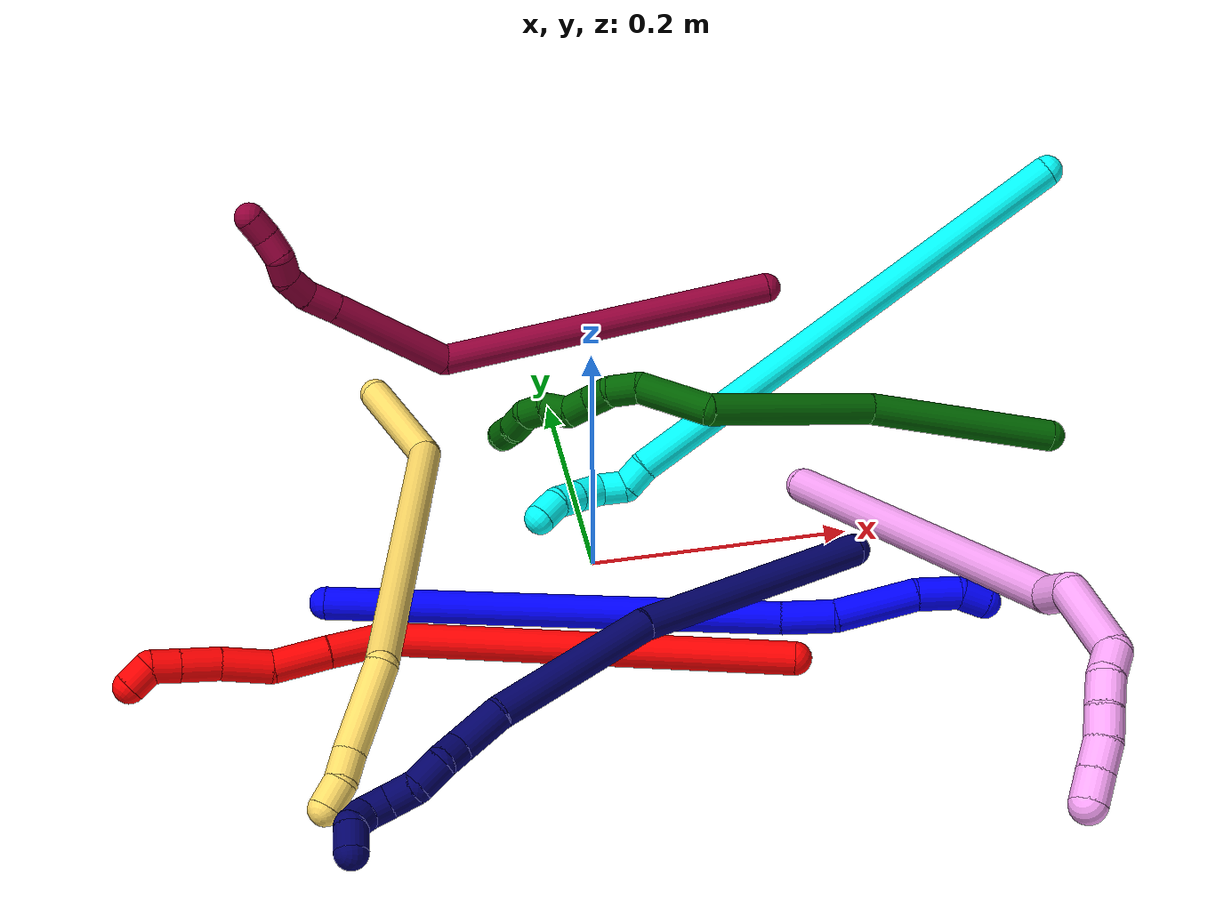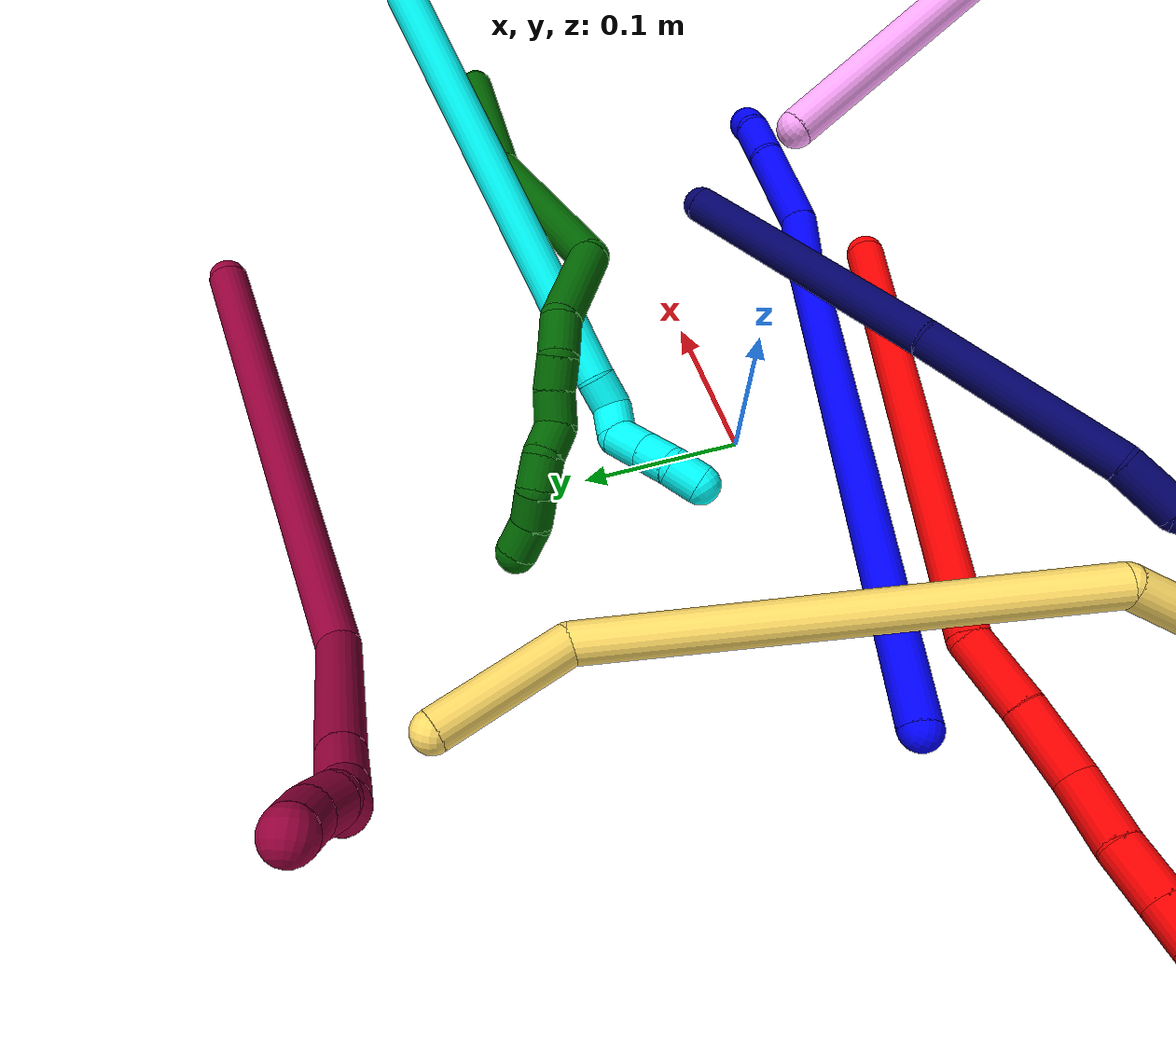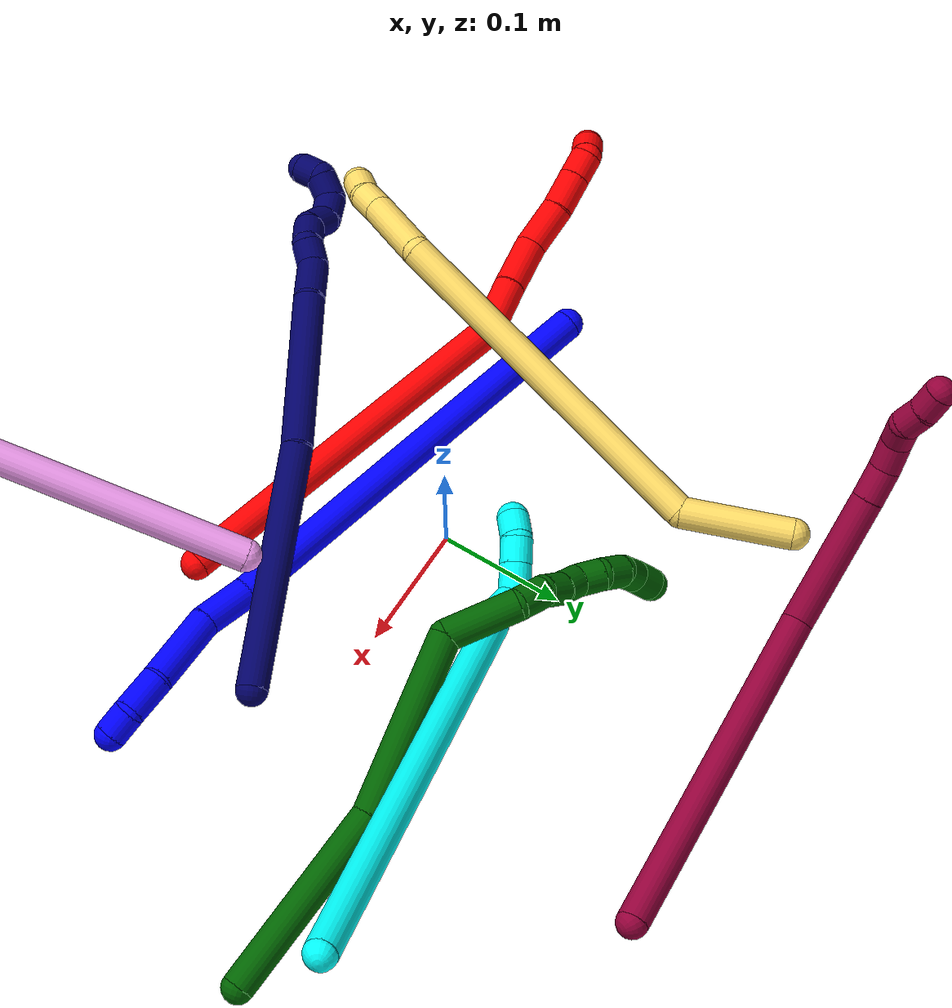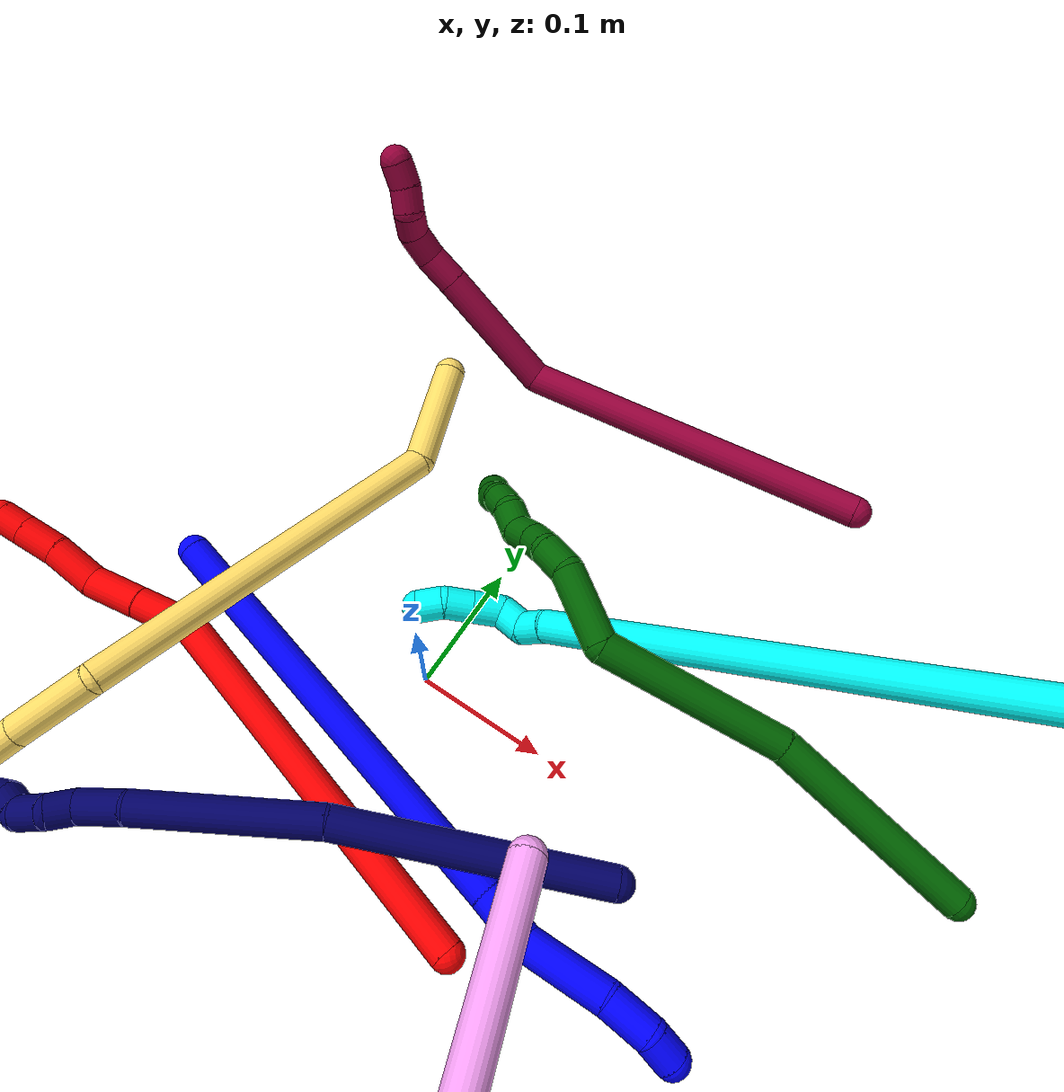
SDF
<sdf version="1.7">
 <world name="default">
  <plugin name="TubeGeneratorPlugin" filename="libtube_generator_plugin.so"/>
  <model name="photoneo_s_sensor">
   <static>1</static>
   <pose>0 0 2 1.57079 1.57079 3.14159</pose>
   <link name="link">
    <inertial><mass>0.1</mass></inertial>
    <sensor name="sensor" type="depth">
     <update_rate>30</update_rate>
     <camera>
      <horizontal_fov>1.22</horizontal_fov>
      <image><width>1920</width><height>1200</height><format>B8G8R8</format></image>
      <clip><near>0.1</near><far>4</far></clip>
      <depth_camera><output>points</output></depth_camera>
     </camera>
     <plugin name="camera_plugin" filename="libgazebo_ros_depth_camera.so">
      <baseline>0.2</baseline>
      <alwaysOn>1</alwaysOn>
      <updateRate>0.0</updateRate>
      <cameraName>camera_ir</cameraName>
      <imageTopicName>/camera/color/image_raw</imageTopicName>
      <cameraInfoTopicName>/camera/color/camera_info</cameraInfoTopicName>
      <depthImageTopicName>/camera/depth/image_raw</depthImageTopicName>
      <depthImageCameraInfoTopicName>/camera/depth/camera_info</depthImageCameraInfoTopicName>
      <pointCloudTopicName>/camera/depth/points</pointCloudTopicName>
      <frameName>fr_optical</frameName>
      <pointCloudCutoff>0.1</pointCloudCutoff>
      <pointCloudCutoffMax>2.0</pointCloudCutoffMax>
      <distortionK1>0</distortionK1>
      <distortionK2>0</distortionK2>
      <distortionK3>0</distortionK3>
      <distortionT1>0</distortionT1>
      <distortionT2>0</distortionT2>
      <CxPrime>0</CxPrime>
      <Cx>0</Cx>
      <Cy>0</Cy>
      <focalLength>0</focalLength>
      <hackBaseline>0</hackBaseline>
     </plugin>
    </sensor>
   </link>
  </model>
  <gravity>0 0 -9.8</gravity>
  <magnetic_field>6e-06 2.3e-05 -4.2e-05</magnetic_field>
  <atmosphere type="adiabatic"/>
  <physics name="default_physics" default="0" type="ode">
   <max_step_size>0.003</max_step_size>
   <real_time_factor>1</real_time_factor>
   <real_time_update_rate>1000</real_time_update_rate>
   <max_contacts>10000</max_contacts>
   <ode>
    <solver>
     <type>quick</type>
     <iters>100</iters>
     <sor>1.3</sor>
     <use_dynamic_moi_rescaling>0</use_dynamic_moi_rescaling>
    </solver>
    <constraints>
     <contact_max_correcting_vel>0</contact_max_correcting_vel>
     <contact_surface_layer>0.001</contact_surface_layer>
     <cfm>0</cfm>
     <erp>0.2</erp>
    </constraints>
   </ode>
  </physics>
  <scene><ambient>0.4 0.4 0.4 1</ambient><background>0.7 0.7 0.7 1</background><shadows>0</shadows></scene>
  <audio><device>default</device></audio>
  <spherical_coordinates>
   <surface_model>EARTH_WGS84</surface_model>
   <latitude_deg>0</latitude_deg>
   <longitude_deg>0</longitude_deg>
   <elevation>0</elevation>
   <heading_deg>0</heading_deg>
  </spherical_coordinates>
  <model name="bin">
   <static>1</static>
   <link name="bottom">
    <collision name="collision-bottom">
     <pose>0 0 -0.01 0 -0 0</pose>
     <geometry><box><size>0.8 0.6 0.02</size></box></geometry>
     <surface>
      <friction><ode><mu>100</mu><mu2>100</mu2></ode></friction>
      <contact><collide_bitmask>65535</collide_bitmask></contact>
     </surface>
    </collision>
   </link>
   <link name="west_wall">
    <collision name="collision-west_wall">
     <pose>-0.41 0 0.1 0 -0 0</pose>
     <geometry><box><size>0.02 0.6 0.2</size></box></geometry>
     <surface>
      <friction><ode><mu>100</mu><mu2>100</mu2></ode></friction>
      <contact><collide_bitmask>65535</collide_bitmask></contact>
     </surface>
    </collision>
   </link>
   <link name="east_wall">
    <collision name="collision-east_wall">
     <pose>0.41 0 0.1 0 -0 0</pose>
     <geometry><box><size>0.02 0.6 0.2</size></box></geometry>
     <surface>
      <friction><ode><mu>100</mu><mu2>100</mu2></ode></friction>
      <contact><collide_bitmask>65535</collide_bitmask></contact>
     </surface>
    </collision>
   </link>
   <link name="south_wall">
    <collision name="collision-south_wall">
     <pose>0 -0.31 0.1 0 -0 0</pose>
     <geometry><box><size>0.8 0.02 0.2</size></box></geometry>
     <surface>
      <friction><ode><mu>100</mu><mu2>100</mu2></ode></friction>
      <contact><collide_bitmask>65535</collide_bitmask></contact>
     </surface>
    </collision>
   </link>
   <link name="north_wall">
    <collision name="collision-north_wall">
     <pose>0 0.31 0.1 0 -0 0</pose>
     <geometry><box><size>0.8 0.02 0.2</size></box></geometry>
     <surface>
      <friction><ode><mu>100</mu><mu2>100</mu2></ode></friction>
      <contact><collide_bitmask>65535</collide_bitmask></contact>
     </surface>
    </collision>
   </link>
  </model>
  <model name="1">
   <static>0</static>
   <link name="1">
    <collision name="collision-cylinder-e_1_1_4">
     <pose>0.16223 -0.052903 -0.01515 1.84971 1.24377 1.52041</pose>
     <geometry><cylinder><radius>0.0125</radius><length>0.342619</length></cylinder></geometry>
     <surface>
      <friction><ode><mu>1.16</mu><mu2>1.16</mu2><slip1>0</slip1><slip2>0</slip2></ode></friction>
      <contact><ode><kp>1e+06</kp><kd>1</kd><max_vel>0</max_vel><min_depth>0.001</min_depth></ode></contact>
     </surface>
    </collision>
    <visual name="visual-cylinder-e_1_1_4">
     <pose>0.16223 -0.052903 -0.01515 1.84971 1.24377 1.52041</pose>
     <geometry><cylinder><radius>0.0125</radius><length>0.342619</length></cylinder></geometry>
     <material><ambient>0 0 1 1</ambient></material>
    </visual>
    <collision name="collision-cylinder-e_2_4_5">
     <pose>0.344215 -0.109629 -0.032409 2.07479 1.35322 1.87354</pose>
     <geometry><cylinder><radius>0.0125</radius><length>0.040462</length></cylinder></geometry>
     <surface>
      <friction><ode><mu>1.16</mu><mu2>1.16</mu2><slip1>0</slip1><slip2>0</slip2></ode></friction>
      <contact><ode><kp>1e+06</kp><kd>1</kd><max_vel>0</max_vel><min_depth>0.001</min_depth></ode></contact>
     </surface>
    </collision>
    <visual name="visual-cylinder-e_2_4_5">
     <pose>0.344215 -0.109629 -0.032409 2.07479 1.35322 1.87354</pose>
     <geometry><cylinder><radius>0.0125</radius><length>0.040462</length></cylinder></geometry>
     <material><ambient>0 0 1 1</ambient></material>
    </visual>
    <collision name="collision-cylinder-e_3_5_6">
     <pose>0.392017 -0.120765 -0.046249 2.58425 1.11291 2.27935</pose>
     <geometry><cylinder><radius>0.0125</radius><length>0.062539</length></cylinder></geometry>
     <surface>
      <friction><ode><mu>1.16</mu><mu2>1.16</mu2><slip1>0</slip1><slip2>0</slip2></ode></friction>
      <contact><ode><kp>1e+06</kp><kd>1</kd><max_vel>0</max_vel><min_depth>0.001</min_depth></ode></contact>
     </surface>
    </collision>
    <visual name="visual-cylinder-e_3_5_6">
     <pose>0.392017 -0.120765 -0.046249 2.58425 1.11291 2.27935</pose>
     <geometry><cylinder><radius>0.0125</radius><length>0.062539</length></cylinder></geometry>
     <material><ambient>0 0 1 1</ambient></material>
    </visual>
    <collision name="collision-cylinder-e_4_6_7">
     <pose>0.434695 -0.134456 -0.061545 2.08031 1.10753 1.62309</pose>
     <geometry><cylinder><radius>0.0125</radius><length>0.032707</length></cylinder></geometry>
     <surface>
      <friction><ode><mu>1.16</mu><mu2>1.16</mu2><slip1>0</slip1><slip2>0</slip2></ode></friction>
      <contact><ode><kp>1e+06</kp><kd>1</kd><max_vel>0</max_vel><min_depth>0.001</min_depth></ode></contact>
     </surface>
    </collision>
    <visual name="visual-cylinder-e_4_6_7">
     <pose>0.434695 -0.134456 -0.061545 2.08031 1.10753 1.62309</pose>
     <geometry><cylinder><radius>0.0125</radius><length>0.032707</length></cylinder></geometry>
     <material><ambient>0 0 1 1</ambient></material>
    </visual>
    <collision name="collision-cylinder-e_5_7_2">
     <pose>0.457489 -0.147947 -0.064644 1.50554 0.853102 0.804966</pose>
     <geometry><cylinder><radius>0.0125</radius><length>0.021673</length></cylinder></geometry>
     <surface>
      <friction><ode><mu>1.16</mu><mu2>1.16</mu2><slip1>0</slip1><slip2>0</slip2></ode></friction>
      <contact><ode><kp>1e+06</kp><kd>1</kd><max_vel>0</max_vel><min_depth>0.001</min_depth></ode></contact>
     </surface>
    </collision>
    <visual name="visual-cylinder-e_5_7_2">
     <pose>0.457489 -0.147947 -0.064644 1.50554 0.853102 0.804966</pose>
     <geometry><cylinder><radius>0.0125</radius><length>0.021673</length></cylinder></geometry>
     <material><ambient>0 0 1 1</ambient></material>
    </visual>
    <collision name="collision-sphere-2">
     <pose>0.465652 -0.155059 -0.06418 0 -0 0</pose>
     <geometry><sphere><radius>0.0125</radius></sphere></geometry>
     <surface>
      <friction><ode><mu>1.16</mu><mu2>1.16</mu2><slip1>0</slip1><slip2>0</slip2></ode></friction>
      <contact><ode><kp>1e+06</kp><kd>1</kd><max_vel>0</max_vel><min_depth>0.001</min_depth></ode></contact>
     </surface>
    </collision>
    <visual name="visual-sphere-2">
     <pose>0.465652 -0.155059 -0.06418 0 -0 0</pose>
     <geometry><sphere><radius>0.0125</radius></sphere></geometry>
     <material><ambient>0 0 1 1</ambient></material>
    </visual>
    <collision name="collision-sphere-7">
     <pose>0.449325 -0.140835 -0.065109 0 -0 0</pose>
     <geometry><sphere><radius>0.0125</radius></sphere></geometry>
     <surface>
      <friction><ode><mu>1.16</mu><mu2>1.16</mu2><slip1>0</slip1><slip2>0</slip2></ode></friction>
      <contact><ode><kp>1e+06</kp><kd>1</kd><max_vel>0</max_vel><min_depth>0.001</min_depth></ode></contact>
     </surface>
    </collision>
    <visual name="visual-sphere-7">
     <pose>0.449325 -0.140835 -0.065109 0 -0 0</pose>
     <geometry><sphere><radius>0.0125</radius></sphere></geometry>
     <material><ambient>0 0 1 1</ambient></material>
    </visual>
    <collision name="collision-sphere-6">
     <pose>0.420065 -0.128076 -0.05798 0 -0 0</pose>
     <geometry><sphere><radius>0.0125</radius></sphere></geometry>
     <surface>
      <friction><ode><mu>1.16</mu><mu2>1.16</mu2><slip1>0</slip1><slip2>0</slip2></ode></friction>
      <contact><ode><kp>1e+06</kp><kd>1</kd><max_vel>0</max_vel><min_depth>0.001</min_depth></ode></contact>
     </surface>
    </collision>
    <visual name="visual-sphere-6">
     <pose>0.420065 -0.128076 -0.05798 0 -0 0</pose>
     <geometry><sphere><radius>0.0125</radius></sphere></geometry>
     <material><ambient>0 0 1 1</ambient></material>
    </visual>
    <collision name="collision-sphere-5">
     <pose>0.363969 -0.113453 -0.034518 0 -0 0</pose>
     <geometry><sphere><radius>0.0125</radius></sphere></geometry>
     <surface>
      <friction><ode><mu>1.16</mu><mu2>1.16</mu2><slip1>0</slip1><slip2>0</slip2></ode></friction>
      <contact><ode><kp>1e+06</kp><kd>1</kd><max_vel>0</max_vel><min_depth>0.001</min_depth></ode></contact>
     </surface>
    </collision>
    <visual name="visual-sphere-5">
     <pose>0.363969 -0.113453 -0.034518 0 -0 0</pose>
     <geometry><sphere><radius>0.0125</radius></sphere></geometry>
     <material><ambient>0 0 1 1</ambient></material>
    </visual>
    <collision name="collision-sphere-1">
     <geometry><sphere><radius>0.0125</radius></sphere></geometry>
     <surface>
      <friction><ode><mu>1.16</mu><mu2>1.16</mu2><slip1>0</slip1><slip2>0</slip2></ode></friction>
      <contact><ode><kp>1e+06</kp><kd>1</kd><max_vel>0</max_vel><min_depth>0.001</min_depth></ode></contact>
     </surface>
    </collision>
    <visual name="visual-sphere-1">
     <geometry><sphere><radius>0.0125</radius></sphere></geometry>
     <material><ambient>0 0 1 1</ambient></material>
    </visual>
    <collision name="collision-sphere-4">
     <pose>0.32446 -0.105805 -0.0303 0 -0 0</pose>
     <geometry><sphere><radius>0.0125</radius></sphere></geometry>
     <surface>
      <friction><ode><mu>1.16</mu><mu2>1.16</mu2><slip1>0</slip1><slip2>0</slip2></ode></friction>
      <contact><ode><kp>1e+06</kp><kd>1</kd><max_vel>0</max_vel><min_depth>0.001</min_depth></ode></contact>
     </surface>
    </collision>
    <visual name="visual-sphere-4">
     <pose>0.32446 -0.105805 -0.0303 0 -0 0</pose>
     <geometry><sphere><radius>0.0125</radius></sphere></geometry>
     <material><ambient>0 0 1 1</ambient></material>
    </visual>
    <inertial>
     <pose>0.23632 -0.075436 -0.025617 0 -0 0</pose>
     <mass>0.5</mass>
     <inertia>
      <ixx>0.001176</ixx>
      <ixy>0</ixy>
      <ixz>0</ixz>
      <iyy>0.004124</iyy>
      <iyz>0</iyz>
      <izz>-0.002176</izz>
     </inertia>
    </inertial>
   </link>
   <pose>-0.208164 -0.018718 0.0115 1.96521 -0.259199 -0.443312</pose>
  </model>
  <model name="2">
   <static>0</static>
   <link name="2">
    <collision name="collision-cylinder-e_1_1_4">
     <pose>-0.094312 0.08413 0.083719 -0.787842 -0.671455 0.28806</pose>
     <geometry><cylinder><radius>0.0125</radius><length>0.303193</length></cylinder></geometry>
     <surface>
      <friction><ode><mu>1.16</mu><mu2>1.16</mu2><slip1>0</slip1><slip2>0</slip2></ode></friction>
      <contact><ode><kp>1e+06</kp><kd>1</kd><max_vel>0</max_vel><min_depth>0.001</min_depth></ode></contact>
     </surface>
    </collision>
    <visual name="visual-cylinder-e_1_1_4">
     <pose>-0.094312 0.08413 0.083719 -0.787842 -0.671455 0.28806</pose>
     <geometry><cylinder><radius>0.0125</radius><length>0.303193</length></cylinder></geometry>
     <material><ambient>1 0 0 1</ambient></material>
    </visual>
    <collision name="collision-cylinder-e_2_4_5">
     <pose>-0.194527 0.180614 0.18487 -0.616579 -0.269541 0.086303</pose>
     <geometry><cylinder><radius>0.0125</radius><length>0.044331</length></cylinder></geometry>
     <surface>
      <friction><ode><mu>1.16</mu><mu2>1.16</mu2><slip1>0</slip1><slip2>0</slip2></ode></friction>
      <contact><ode><kp>1e+06</kp><kd>1</kd><max_vel>0</max_vel><min_depth>0.001</min_depth></ode></contact>
     </surface>
    </collision>
    <visual name="visual-cylinder-e_2_4_5">
     <pose>-0.194527 0.180614 0.18487 -0.616579 -0.269541 0.086303</pose>
     <geometry><cylinder><radius>0.0125</radius><length>0.044331</length></cylinder></geometry>
     <material><ambient>1 0 0 1</ambient></material>
    </visual>
    <collision name="collision-cylinder-e_3_5_6">
     <pose>-0.206873 0.203748 0.219395 -0.56266 -0.308658 0.089855</pose>
     <geometry><cylinder><radius>0.0125</radius><length>0.042424</length></cylinder></geometry>
     <surface>
      <friction><ode><mu>1.16</mu><mu2>1.16</mu2><slip1>0</slip1><slip2>0</slip2></ode></friction>
      <contact><ode><kp>1e+06</kp><kd>1</kd><max_vel>0</max_vel><min_depth>0.001</min_depth></ode></contact>
     </surface>
    </collision>
    <visual name="visual-cylinder-e_3_5_6">
     <pose>-0.206873 0.203748 0.219395 -0.56266 -0.308658 0.089855</pose>
     <geometry><cylinder><radius>0.0125</radius><length>0.042424</length></cylinder></geometry>
     <material><ambient>1 0 0 1</ambient></material>
    </visual>
    <collision name="collision-cylinder-e_4_6_7">
     <pose>-0.22067 0.228337 0.247556 -0.895165 -0.393805 0.190956</pose>
     <geometry><cylinder><radius>0.0125</radius><length>0.038325</length></cylinder></geometry>
     <surface>
      <friction><ode><mu>1.16</mu><mu2>1.16</mu2><slip1>0</slip1><slip2>0</slip2></ode></friction>
      <contact><ode><kp>1e+06</kp><kd>1</kd><max_vel>0</max_vel><min_depth>0.001</min_depth></ode></contact>
     </surface>
    </collision>
    <visual name="visual-cylinder-e_4_6_7">
     <pose>-0.22067 0.228337 0.247556 -0.895165 -0.393805 0.190956</pose>
     <geometry><cylinder><radius>0.0125</radius><length>0.038325</length></cylinder></geometry>
     <material><ambient>1 0 0 1</ambient></material>
    </visual>
    <collision name="collision-cylinder-e_5_7_8">
     <pose>-0.232422 0.25248 0.26864 -0.801005 -0.29668 0.126371</pose>
     <geometry><cylinder><radius>0.0125</radius><length>0.030101</length></cylinder></geometry>
     <surface>
      <friction><ode><mu>1.16</mu><mu2>1.16</mu2><slip1>0</slip1><slip2>0</slip2></ode></friction>
      <contact><ode><kp>1e+06</kp><kd>1</kd><max_vel>0</max_vel><min_depth>0.001</min_depth></ode></contact>
     </surface>
    </collision>
    <visual name="visual-cylinder-e_5_7_8">
     <pose>-0.232422 0.25248 0.26864 -0.801005 -0.29668 0.126371</pose>
     <geometry><cylinder><radius>0.0125</radius><length>0.030101</length></cylinder></geometry>
     <material><ambient>1 0 0 1</ambient></material>
    </visual>
    <collision name="collision-cylinder-e_6_8_9">
     <pose>-0.239971 0.270197 0.28567 -0.811016 -0.29988 0.129531</pose>
     <geometry><cylinder><radius>0.0125</radius><length>0.021316</length></cylinder></geometry>
     <surface>
      <friction><ode><mu>1.16</mu><mu2>1.16</mu2><slip1>0</slip1><slip2>0</slip2></ode></friction>
      <contact><ode><kp>1e+06</kp><kd>1</kd><max_vel>0</max_vel><min_depth>0.001</min_depth></ode></contact>
     </surface>
    </collision>
    <visual name="visual-cylinder-e_6_8_9">
     <pose>-0.239971 0.270197 0.28567 -0.811016 -0.29988 0.129531</pose>
     <geometry><cylinder><radius>0.0125</radius><length>0.021316</length></cylinder></geometry>
     <material><ambient>1 0 0 1</ambient></material>
    </visual>
    <collision name="collision-cylinder-e_7_9_2">
     <pose>-0.244843 0.27773 0.30269 -0.015121 -0.170557 0.001293</pose>
     <geometry><cylinder><radius>0.0125</radius><length>0.020311</length></cylinder></geometry>
     <surface>
      <friction><ode><mu>1.16</mu><mu2>1.16</mu2><slip1>0</slip1><slip2>0</slip2></ode></friction>
      <contact><ode><kp>1e+06</kp><kd>1</kd><max_vel>0</max_vel><min_depth>0.001</min_depth></ode></contact>
     </surface>
    </collision>
    <visual name="visual-cylinder-e_7_9_2">
     <pose>-0.244843 0.27773 0.30269 -0.015121 -0.170557 0.001293</pose>
     <geometry><cylinder><radius>0.0125</radius><length>0.020311</length></cylinder></geometry>
     <material><ambient>1 0 0 1</ambient></material>
    </visual>
    <collision name="collision-sphere-2">
     <pose>-0.246566 0.277882 0.312697 0 -0 0</pose>
     <geometry><sphere><radius>0.0125</radius></sphere></geometry>
     <surface>
      <friction><ode><mu>1.16</mu><mu2>1.16</mu2><slip1>0</slip1><slip2>0</slip2></ode></friction>
      <contact><ode><kp>1e+06</kp><kd>1</kd><max_vel>0</max_vel><min_depth>0.001</min_depth></ode></contact>
     </surface>
    </collision>
    <visual name="visual-sphere-2">
     <pose>-0.246566 0.277882 0.312697 0 -0 0</pose>
     <geometry><sphere><radius>0.0125</radius></sphere></geometry>
     <material><ambient>1 0 0 1</ambient></material>
    </visual>
    <collision name="collision-sphere-9">
     <pose>-0.243119 0.277579 0.292683 0 -0 0</pose>
     <geometry><sphere><radius>0.0125</radius></sphere></geometry>
     <surface>
      <friction><ode><mu>1.16</mu><mu2>1.16</mu2><slip1>0</slip1><slip2>0</slip2></ode></friction>
      <contact><ode><kp>1e+06</kp><kd>1</kd><max_vel>0</max_vel><min_depth>0.001</min_depth></ode></contact>
     </surface>
    </collision>
    <visual name="visual-sphere-9">
     <pose>-0.243119 0.277579 0.292683 0 -0 0</pose>
     <geometry><sphere><radius>0.0125</radius></sphere></geometry>
     <material><ambient>1 0 0 1</ambient></material>
    </visual>
    <collision name="collision-sphere-4">
     <pose>-0.188625 0.168259 0.167439 0 -0 0</pose>
     <geometry><sphere><radius>0.0125</radius></sphere></geometry>
     <surface>
      <friction><ode><mu>1.16</mu><mu2>1.16</mu2><slip1>0</slip1><slip2>0</slip2></ode></friction>
      <contact><ode><kp>1e+06</kp><kd>1</kd><max_vel>0</max_vel><min_depth>0.001</min_depth></ode></contact>
     </surface>
    </collision>
    <visual name="visual-sphere-4">
     <pose>-0.188625 0.168259 0.167439 0 -0 0</pose>
     <geometry><sphere><radius>0.0125</radius></sphere></geometry>
     <material><ambient>1 0 0 1</ambient></material>
    </visual>
    <collision name="collision-sphere-1">
     <geometry><sphere><radius>0.0125</radius></sphere></geometry>
     <surface>
      <friction><ode><mu>1.16</mu><mu2>1.16</mu2><slip1>0</slip1><slip2>0</slip2></ode></friction>
      <contact><ode><kp>1e+06</kp><kd>1</kd><max_vel>0</max_vel><min_depth>0.001</min_depth></ode></contact>
     </surface>
    </collision>
    <visual name="visual-sphere-1">
     <geometry><sphere><radius>0.0125</radius></sphere></geometry>
     <material><ambient>1 0 0 1</ambient></material>
    </visual>
    <collision name="collision-sphere-8">
     <pose>-0.236822 0.262815 0.278657 0 -0 0</pose>
     <geometry><sphere><radius>0.0125</radius></sphere></geometry>
     <surface>
      <friction><ode><mu>1.16</mu><mu2>1.16</mu2><slip1>0</slip1><slip2>0</slip2></ode></friction>
      <contact><ode><kp>1e+06</kp><kd>1</kd><max_vel>0</max_vel><min_depth>0.001</min_depth></ode></contact>
     </surface>
    </collision>
    <visual name="visual-sphere-8">
     <pose>-0.236822 0.262815 0.278657 0 -0 0</pose>
     <geometry><sphere><radius>0.0125</radius></sphere></geometry>
     <material><ambient>1 0 0 1</ambient></material>
    </visual>
    <collision name="collision-sphere-5">
     <pose>-0.200429 0.192968 0.202301 0 -0 0</pose>
     <geometry><sphere><radius>0.0125</radius></sphere></geometry>
     <surface>
      <friction><ode><mu>1.16</mu><mu2>1.16</mu2><slip1>0</slip1><slip2>0</slip2></ode></friction>
      <contact><ode><kp>1e+06</kp><kd>1</kd><max_vel>0</max_vel><min_depth>0.001</min_depth></ode></contact>
     </surface>
    </collision>
    <visual name="visual-sphere-5">
     <pose>-0.200429 0.192968 0.202301 0 -0 0</pose>
     <geometry><sphere><radius>0.0125</radius></sphere></geometry>
     <material><ambient>1 0 0 1</ambient></material>
    </visual>
    <collision name="collision-sphere-6">
     <pose>-0.213317 0.214529 0.236489 0 -0 0</pose>
     <geometry><sphere><radius>0.0125</radius></sphere></geometry>
     <surface>
      <friction><ode><mu>1.16</mu><mu2>1.16</mu2><slip1>0</slip1><slip2>0</slip2></ode></friction>
      <contact><ode><kp>1e+06</kp><kd>1</kd><max_vel>0</max_vel><min_depth>0.001</min_depth></ode></contact>
     </surface>
    </collision>
    <visual name="visual-sphere-6">
     <pose>-0.213317 0.214529 0.236489 0 -0 0</pose>
     <geometry><sphere><radius>0.0125</radius></sphere></geometry>
     <material><ambient>1 0 0 1</ambient></material>
    </visual>
    <collision name="collision-sphere-7">
     <pose>-0.228022 0.242145 0.258622 0 -0 0</pose>
     <geometry><sphere><radius>0.0125</radius></sphere></geometry>
     <surface>
      <friction><ode><mu>1.16</mu><mu2>1.16</mu2><slip1>0</slip1><slip2>0</slip2></ode></friction>
      <contact><ode><kp>1e+06</kp><kd>1</kd><max_vel>0</max_vel><min_depth>0.001</min_depth></ode></contact>
     </surface>
    </collision>
    <visual name="visual-sphere-7">
     <pose>-0.228022 0.242145 0.258622 0 -0 0</pose>
     <geometry><sphere><radius>0.0125</radius></sphere></geometry>
     <material><ambient>1 0 0 1</ambient></material>
    </visual>
    <inertial>
     <pose>-0.143072 0.139818 0.145394 0 -0 0</pose>
     <mass>0.5</mass>
     <inertia>
      <ixx>0.002284</ixx>
      <ixy>0</ixy>
      <ixz>0</ixz>
      <iyy>0.002439</iyy>
      <iyz>0</iyz>
      <izz>0.000173</izz>
     </inertia>
    </inertial>
   </link>
   <pose>0.123875 -0.145958 0.011773 2.05778 -0.35353 -1.1046</pose>
  </model>
  <model name="3">
   <static>0</static>
   <link name="3">
    <collision name="collision-cylinder-e_1_1_4">
     <pose>-0.028551 -0.020709 -0.193059 3.03473 -0.145999 -1.87874</pose>
     <geometry><cylinder><radius>0.0125</radius><length>0.392508</length></cylinder></geometry>
     <surface>
      <friction><ode><mu>1.16</mu><mu2>1.16</mu2><slip1>0</slip1><slip2>0</slip2></ode></friction>
      <contact><ode><kp>1e+06</kp><kd>1</kd><max_vel>0</max_vel><min_depth>0.001</min_depth></ode></contact>
     </surface>
    </collision>
    <visual name="visual-cylinder-e_1_1_4">
     <pose>-0.028551 -0.020709 -0.193059 3.03473 -0.145999 -1.87874</pose>
     <geometry><cylinder><radius>0.0125</radius><length>0.392508</length></cylinder></geometry>
     <material><ambient>0.003922 1 0.996078 1</ambient></material>
    </visual>
    <collision name="collision-cylinder-e_2_4_5">
     <pose>-0.057775 -0.040374 -0.396617 -3.04256 -0.06368 1.1425</pose>
     <geometry><cylinder><radius>0.0125</radius><length>0.021145</length></cylinder></geometry>
     <surface>
      <friction><ode><mu>1.16</mu><mu2>1.16</mu2><slip1>0</slip1><slip2>0</slip2></ode></friction>
      <contact><ode><kp>1e+06</kp><kd>1</kd><max_vel>0</max_vel><min_depth>0.001</min_depth></ode></contact>
     </surface>
    </collision>
    <visual name="visual-cylinder-e_2_4_5">
     <pose>-0.057775 -0.040374 -0.396617 -3.04256 -0.06368 1.1425</pose>
     <geometry><cylinder><radius>0.0125</radius><length>0.021145</length></cylinder></geometry>
     <material><ambient>0.003922 1 0.996078 1</ambient></material>
    </visual>
    <collision name="collision-cylinder-e_3_5_6">
     <pose>-0.06285 -0.044604 -0.415414 2.57541 -0.420955 -1.2669</pose>
     <geometry><cylinder><radius>0.0125</radius><length>0.021543</length></cylinder></geometry>
     <surface>
      <friction><ode><mu>1.16</mu><mu2>1.16</mu2><slip1>0</slip1><slip2>0</slip2></ode></friction>
      <contact><ode><kp>1e+06</kp><kd>1</kd><max_vel>0</max_vel><min_depth>0.001</min_depth></ode></contact>
     </surface>
    </collision>
    <visual name="visual-cylinder-e_3_5_6">
     <pose>-0.06285 -0.044604 -0.415414 2.57541 -0.420955 -1.2669</pose>
     <geometry><cylinder><radius>0.0125</radius><length>0.021543</length></cylinder></geometry>
     <material><ambient>0.003922 1 0.996078 1</ambient></material>
    </visual>
    <collision name="collision-cylinder-e_4_6_7">
     <pose>-0.06355 -0.057524 -0.432239 2.41067 0.312545 0.781191</pose>
     <geometry><cylinder><radius>0.0125</radius><length>0.024074</length></cylinder></geometry>
     <surface>
      <friction><ode><mu>1.16</mu><mu2>1.16</mu2><slip1>0</slip1><slip2>0</slip2></ode></friction>
      <contact><ode><kp>1e+06</kp><kd>1</kd><max_vel>0</max_vel><min_depth>0.001</min_depth></ode></contact>
     </surface>
    </collision>
    <visual name="visual-cylinder-e_4_6_7">
     <pose>-0.06355 -0.057524 -0.432239 2.41067 0.312545 0.781191</pose>
     <geometry><cylinder><radius>0.0125</radius><length>0.024074</length></cylinder></geometry>
     <material><ambient>0.003922 1 0.996078 1</ambient></material>
    </visual>
    <collision name="collision-cylinder-e_5_7_8">
     <pose>-0.056695 -0.071696 -0.448073 2.41257 0.31146 0.780706</pose>
     <geometry><cylinder><radius>0.0125</radius><length>0.020582</length></cylinder></geometry>
     <surface>
      <friction><ode><mu>1.16</mu><mu2>1.16</mu2><slip1>0</slip1><slip2>0</slip2></ode></friction>
      <contact><ode><kp>1e+06</kp><kd>1</kd><max_vel>0</max_vel><min_depth>0.001</min_depth></ode></contact>
     </surface>
    </collision>
    <visual name="visual-cylinder-e_5_7_8">
     <pose>-0.056695 -0.071696 -0.448073 2.41257 0.31146 0.780706</pose>
     <geometry><cylinder><radius>0.0125</radius><length>0.020582</length></cylinder></geometry>
     <material><ambient>0.003922 1 0.996078 1</ambient></material>
    </visual>
    <collision name="collision-cylinder-e_6_8_2">
     <pose>-0.049851 -0.080796 -0.464392 2.86331 0.375064 1.87003</pose>
     <geometry><cylinder><radius>0.0125</radius><length>0.020147</length></cylinder></geometry>
     <surface>
      <friction><ode><mu>1.16</mu><mu2>1.16</mu2><slip1>0</slip1><slip2>0</slip2></ode></friction>
      <contact><ode><kp>1e+06</kp><kd>1</kd><max_vel>0</max_vel><min_depth>0.001</min_depth></ode></contact>
     </surface>
    </collision>
    <visual name="visual-cylinder-e_6_8_2">
     <pose>-0.049851 -0.080796 -0.464392 2.86331 0.375064 1.87003</pose>
     <geometry><cylinder><radius>0.0125</radius><length>0.020147</length></cylinder></geometry>
     <material><ambient>0.003922 1 0.996078 1</ambient></material>
    </visual>
    <collision name="collision-sphere-2">
     <pose>-0.046161 -0.083371 -0.473404 0 -0 0</pose>
     <geometry><sphere><radius>0.0125</radius></sphere></geometry>
     <surface>
      <friction><ode><mu>1.16</mu><mu2>1.16</mu2><slip1>0</slip1><slip2>0</slip2></ode></friction>
      <contact><ode><kp>1e+06</kp><kd>1</kd><max_vel>0</max_vel><min_depth>0.001</min_depth></ode></contact>
     </surface>
    </collision>
    <visual name="visual-sphere-2">
     <pose>-0.046161 -0.083371 -0.473404 0 -0 0</pose>
     <geometry><sphere><radius>0.0125</radius></sphere></geometry>
     <material><ambient>0.003922 1 0.996078 1</ambient></material>
    </visual>
    <collision name="collision-sphere-4">
     <pose>-0.057102 -0.041417 -0.386118 0 -0 0</pose>
     <geometry><sphere><radius>0.0125</radius></sphere></geometry>
     <surface>
      <friction><ode><mu>1.16</mu><mu2>1.16</mu2><slip1>0</slip1><slip2>0</slip2></ode></friction>
      <contact><ode><kp>1e+06</kp><kd>1</kd><max_vel>0</max_vel><min_depth>0.001</min_depth></ode></contact>
     </surface>
    </collision>
    <visual name="visual-sphere-4">
     <pose>-0.057102 -0.041417 -0.386118 0 -0 0</pose>
     <geometry><sphere><radius>0.0125</radius></sphere></geometry>
     <material><ambient>0.003922 1 0.996078 1</ambient></material>
    </visual>
    <collision name="collision-sphere-1">
     <geometry><sphere><radius>0.0125</radius></sphere></geometry>
     <surface>
      <friction><ode><mu>1.16</mu><mu2>1.16</mu2><slip1>0</slip1><slip2>0</slip2></ode></friction>
      <contact><ode><kp>1e+06</kp><kd>1</kd><max_vel>0</max_vel><min_depth>0.001</min_depth></ode></contact>
     </surface>
    </collision>
    <visual name="visual-sphere-1">
     <geometry><sphere><radius>0.0125</radius></sphere></geometry>
     <material><ambient>0.003922 1 0.996078 1</ambient></material>
    </visual>
    <collision name="collision-sphere-8">
     <pose>-0.053541 -0.078221 -0.455379 0 -0 0</pose>
     <geometry><sphere><radius>0.0125</radius></sphere></geometry>
     <surface>
      <friction><ode><mu>1.16</mu><mu2>1.16</mu2><slip1>0</slip1><slip2>0</slip2></ode></friction>
      <contact><ode><kp>1e+06</kp><kd>1</kd><max_vel>0</max_vel><min_depth>0.001</min_depth></ode></contact>
     </surface>
    </collision>
    <visual name="visual-sphere-8">
     <pose>-0.053541 -0.078221 -0.455379 0 -0 0</pose>
     <geometry><sphere><radius>0.0125</radius></sphere></geometry>
     <material><ambient>0.003922 1 0.996078 1</ambient></material>
    </visual>
    <collision name="collision-sphere-5">
     <pose>-0.058448 -0.039331 -0.407117 0 -0 0</pose>
     <geometry><sphere><radius>0.0125</radius></sphere></geometry>
     <surface>
      <friction><ode><mu>1.16</mu><mu2>1.16</mu2><slip1>0</slip1><slip2>0</slip2></ode></friction>
      <contact><ode><kp>1e+06</kp><kd>1</kd><max_vel>0</max_vel><min_depth>0.001</min_depth></ode></contact>
     </surface>
    </collision>
    <visual name="visual-sphere-5">
     <pose>-0.058448 -0.039331 -0.407117 0 -0 0</pose>
     <geometry><sphere><radius>0.0125</radius></sphere></geometry>
     <material><ambient>0.003922 1 0.996078 1</ambient></material>
    </visual>
    <collision name="collision-sphere-6">
     <pose>-0.067251 -0.049878 -0.423711 0 -0 0</pose>
     <geometry><sphere><radius>0.0125</radius></sphere></geometry>
     <surface>
      <friction><ode><mu>1.16</mu><mu2>1.16</mu2><slip1>0</slip1><slip2>0</slip2></ode></friction>
      <contact><ode><kp>1e+06</kp><kd>1</kd><max_vel>0</max_vel><min_depth>0.001</min_depth></ode></contact>
     </surface>
    </collision>
    <visual name="visual-sphere-6">
     <pose>-0.067251 -0.049878 -0.423711 0 -0 0</pose>
     <geometry><sphere><radius>0.0125</radius></sphere></geometry>
     <material><ambient>0.003922 1 0.996078 1</ambient></material>
    </visual>
    <collision name="collision-sphere-7">
     <pose>-0.059849 -0.06517 -0.440767 0 -0 0</pose>
     <geometry><sphere><radius>0.0125</radius></sphere></geometry>
     <surface>
      <friction><ode><mu>1.16</mu><mu2>1.16</mu2><slip1>0</slip1><slip2>0</slip2></ode></friction>
      <contact><ode><kp>1e+06</kp><kd>1</kd><max_vel>0</max_vel><min_depth>0.001</min_depth></ode></contact>
     </surface>
    </collision>
    <visual name="visual-sphere-7">
     <pose>-0.059849 -0.06517 -0.440767 0 -0 0</pose>
     <geometry><sphere><radius>0.0125</radius></sphere></geometry>
     <material><ambient>0.003922 1 0.996078 1</ambient></material>
    </visual>
    <inertial>
     <pose>-0.034967 -0.028862 -0.244194 0 -0 0</pose>
     <mass>0.5</mass>
     <inertia>
      <ixx>-0.006278</ixx>
      <ixy>0</ixy>
      <ixz>0</ixz>
      <iyy>-0.003172</iyy>
      <iyz>0</iyz>
      <izz>0.001234</izz>
     </inertia>
    </inertial>
   </link>
   <pose>0.393664 0.15699 0.209743 -1.00072 -0.277897 -1.31661</pose>
  </model>
  <model name="4">
   <static>0</static>
   <link name="4">
    <collision name="collision-cylinder-e_1_1_4">
     <pose>-0.015459 -0.141959 -0.053119 1.92885 -0.101642 -0.146421</pose>
     <geometry><cylinder><radius>0.0125</radius><length>0.304717</length></cylinder></geometry>
     <surface>
      <friction><ode><mu>1.16</mu><mu2>1.16</mu2><slip1>0</slip1><slip2>0</slip2></ode></friction>
      <contact><ode><kp>1e+06</kp><kd>1</kd><max_vel>0</max_vel><min_depth>0.001</min_depth></ode></contact>
     </surface>
    </collision>
    <visual name="visual-cylinder-e_1_1_4">
     <pose>-0.015459 -0.141959 -0.053119 1.92885 -0.101642 -0.146421</pose>
     <geometry><cylinder><radius>0.0125</radius><length>0.304717</length></cylinder></geometry>
     <material><ambient>1 0.65098 0.996078 1</ambient></material>
    </visual>
    <collision name="collision-cylinder-e_2_4_5">
     <pose>-0.034486 -0.293651 -0.114186 2.25556 -0.276622 -0.570747</pose>
     <geometry><cylinder><radius>0.0125</radius><length>0.026124</length></cylinder></geometry>
     <surface>
      <friction><ode><mu>1.16</mu><mu2>1.16</mu2><slip1>0</slip1><slip2>0</slip2></ode></friction>
      <contact><ode><kp>1e+06</kp><kd>1</kd><max_vel>0</max_vel><min_depth>0.001</min_depth></ode></contact>
     </surface>
    </collision>
    <visual name="visual-cylinder-e_2_4_5">
     <pose>-0.034486 -0.293651 -0.114186 2.25556 -0.276622 -0.570747</pose>
     <geometry><cylinder><radius>0.0125</radius><length>0.026124</length></cylinder></geometry>
     <material><ambient>1 0.65098 0.996078 1</ambient></material>
    </visual>
    <collision name="collision-cylinder-e_3_5_6">
     <pose>-0.030695 -0.334409 -0.128688 1.77901 0.228014 0.28059</pose>
     <geometry><cylinder><radius>0.0125</radius><length>0.065105</length></cylinder></geometry>
     <surface>
      <friction><ode><mu>1.16</mu><mu2>1.16</mu2><slip1>0</slip1><slip2>0</slip2></ode></friction>
      <contact><ode><kp>1e+06</kp><kd>1</kd><max_vel>0</max_vel><min_depth>0.001</min_depth></ode></contact>
     </surface>
    </collision>
    <visual name="visual-cylinder-e_3_5_6">
     <pose>-0.030695 -0.334409 -0.128688 1.77901 0.228014 0.28059</pose>
     <geometry><cylinder><radius>0.0125</radius><length>0.065105</length></cylinder></geometry>
     <material><ambient>1 0.65098 0.996078 1</ambient></material>
    </visual>
    <collision name="collision-cylinder-e_4_6_7">
     <pose>-0.015355 -0.372103 -0.13813 1.97939 0.832202 1.18457</pose>
     <geometry><cylinder><radius>0.0125</radius><length>0.021589</length></cylinder></geometry>
     <surface>
      <friction><ode><mu>1.16</mu><mu2>1.16</mu2><slip1>0</slip1><slip2>0</slip2></ode></friction>
      <contact><ode><kp>1e+06</kp><kd>1</kd><max_vel>0</max_vel><min_depth>0.001</min_depth></ode></contact>
     </surface>
    </collision>
    <visual name="visual-cylinder-e_4_6_7">
     <pose>-0.015355 -0.372103 -0.13813 1.97939 0.832202 1.18457</pose>
     <geometry><cylinder><radius>0.0125</radius><length>0.021589</length></cylinder></geometry>
     <material><ambient>1 0.65098 0.996078 1</ambient></material>
    </visual>
    <collision name="collision-cylinder-e_5_7_8">
     <pose>0.000167 -0.38605 -0.140172 1.45511 0.799814 0.720012</pose>
     <geometry><cylinder><radius>0.0125</radius><length>0.021027</length></cylinder></geometry>
     <surface>
      <friction><ode><mu>1.16</mu><mu2>1.16</mu2><slip1>0</slip1><slip2>0</slip2></ode></friction>
      <contact><ode><kp>1e+06</kp><kd>1</kd><max_vel>0</max_vel><min_depth>0.001</min_depth></ode></contact>
     </surface>
    </collision>
    <visual name="visual-cylinder-e_5_7_8">
     <pose>0.000167 -0.38605 -0.140172 1.45511 0.799814 0.720012</pose>
     <geometry><cylinder><radius>0.0125</radius><length>0.021027</length></cylinder></geometry>
     <material><ambient>1 0.65098 0.996078 1</ambient></material>
    </visual>
    <collision name="collision-cylinder-e_6_8_9">
     <pose>0.014983 -0.400119 -0.137172 1.26367 0.795753 0.596874</pose>
     <geometry><cylinder><radius>0.0125</radius><length>0.020367</length></cylinder></geometry>
     <surface>
      <friction><ode><mu>1.16</mu><mu2>1.16</mu2><slip1>0</slip1><slip2>0</slip2></ode></friction>
      <contact><ode><kp>1e+06</kp><kd>1</kd><max_vel>0</max_vel><min_depth>0.001</min_depth></ode></contact>
     </surface>
    </collision>
    <visual name="visual-cylinder-e_6_8_9">
     <pose>0.014983 -0.400119 -0.137172 1.26367 0.795753 0.596874</pose>
     <geometry><cylinder><radius>0.0125</radius><length>0.020367</length></cylinder></geometry>
     <material><ambient>1 0.65098 0.996078 1</ambient></material>
    </visual>
    <collision name="collision-cylinder-e_7_9_10">
     <pose>0.030888 -0.412275 -0.13356 1.30533 0.998637 0.790027</pose>
     <geometry><cylinder><radius>0.0125</radius><length>0.020531</length></cylinder></geometry>
     <surface>
      <friction><ode><mu>1.16</mu><mu2>1.16</mu2><slip1>0</slip1><slip2>0</slip2></ode></friction>
      <contact><ode><kp>1e+06</kp><kd>1</kd><max_vel>0</max_vel><min_depth>0.001</min_depth></ode></contact>
     </surface>
    </collision>
    <visual name="visual-cylinder-e_7_9_10">
     <pose>0.030888 -0.412275 -0.13356 1.30533 0.998637 0.790027</pose>
     <geometry><cylinder><radius>0.0125</radius><length>0.020531</length></cylinder></geometry>
     <material><ambient>1 0.65098 0.996078 1</ambient></material>
    </visual>
    <collision name="collision-cylinder-e_8_10_2">
     <pose>0.048052 -0.423213 -0.130843 1.34877 0.980692 0.806709</pose>
     <geometry><cylinder><radius>0.0125</radius><length>0.02054</length></cylinder></geometry>
     <surface>
      <friction><ode><mu>1.16</mu><mu2>1.16</mu2><slip1>0</slip1><slip2>0</slip2></ode></friction>
      <contact><ode><kp>1e+06</kp><kd>1</kd><max_vel>0</max_vel><min_depth>0.001</min_depth></ode></contact>
     </surface>
    </collision>
    <visual name="visual-cylinder-e_8_10_2">
     <pose>0.048052 -0.423213 -0.130843 1.34877 0.980692 0.806709</pose>
     <geometry><cylinder><radius>0.0125</radius><length>0.02054</length></cylinder></geometry>
     <material><ambient>1 0.65098 0.996078 1</ambient></material>
    </visual>
    <collision name="collision-sphere-2">
     <pose>0.056585 -0.428788 -0.129585 0 -0 0</pose>
     <geometry><sphere><radius>0.0125</radius></sphere></geometry>
     <surface>
      <friction><ode><mu>1.16</mu><mu2>1.16</mu2><slip1>0</slip1><slip2>0</slip2></ode></friction>
      <contact><ode><kp>1e+06</kp><kd>1</kd><max_vel>0</max_vel><min_depth>0.001</min_depth></ode></contact>
     </surface>
    </collision>
    <visual name="visual-sphere-2">
     <pose>0.056585 -0.428788 -0.129585 0 -0 0</pose>
     <geometry><sphere><radius>0.0125</radius></sphere></geometry>
     <material><ambient>1 0.65098 0.996078 1</ambient></material>
    </visual>
    <collision name="collision-sphere-10">
     <pose>0.039519 -0.417639 -0.132101 0 -0 0</pose>
     <geometry><sphere><radius>0.0125</radius></sphere></geometry>
     <surface>
      <friction><ode><mu>1.16</mu><mu2>1.16</mu2><slip1>0</slip1><slip2>0</slip2></ode></friction>
      <contact><ode><kp>1e+06</kp><kd>1</kd><max_vel>0</max_vel><min_depth>0.001</min_depth></ode></contact>
     </surface>
    </collision>
    <visual name="visual-sphere-10">
     <pose>0.039519 -0.417639 -0.132101 0 -0 0</pose>
     <geometry><sphere><radius>0.0125</radius></sphere></geometry>
     <material><ambient>1 0.65098 0.996078 1</ambient></material>
    </visual>
    <collision name="collision-sphere-9">
     <pose>0.022258 -0.406912 -0.135018 0 -0 0</pose>
     <geometry><sphere><radius>0.0125</radius></sphere></geometry>
     <surface>
      <friction><ode><mu>1.16</mu><mu2>1.16</mu2><slip1>0</slip1><slip2>0</slip2></ode></friction>
      <contact><ode><kp>1e+06</kp><kd>1</kd><max_vel>0</max_vel><min_depth>0.001</min_depth></ode></contact>
     </surface>
    </collision>
    <visual name="visual-sphere-9">
     <pose>0.022258 -0.406912 -0.135018 0 -0 0</pose>
     <geometry><sphere><radius>0.0125</radius></sphere></geometry>
     <material><ambient>1 0.65098 0.996078 1</ambient></material>
    </visual>
    <collision name="collision-sphere-4">
     <pose>-0.030919 -0.283919 -0.106238 0 -0 0</pose>
     <geometry><sphere><radius>0.0125</radius></sphere></geometry>
     <surface>
      <friction><ode><mu>1.16</mu><mu2>1.16</mu2><slip1>0</slip1><slip2>0</slip2></ode></friction>
      <contact><ode><kp>1e+06</kp><kd>1</kd><max_vel>0</max_vel><min_depth>0.001</min_depth></ode></contact>
     </surface>
    </collision>
    <visual name="visual-sphere-4">
     <pose>-0.030919 -0.283919 -0.106238 0 -0 0</pose>
     <geometry><sphere><radius>0.0125</radius></sphere></geometry>
     <material><ambient>1 0.65098 0.996078 1</ambient></material>
    </visual>
    <collision name="collision-sphere-1">
     <geometry><sphere><radius>0.0125</radius></sphere></geometry>
     <surface>
      <friction><ode><mu>1.16</mu><mu2>1.16</mu2><slip1>0</slip1><slip2>0</slip2></ode></friction>
      <contact><ode><kp>1e+06</kp><kd>1</kd><max_vel>0</max_vel><min_depth>0.001</min_depth></ode></contact>
     </surface>
    </collision>
    <visual name="visual-sphere-1">
     <geometry><sphere><radius>0.0125</radius></sphere></geometry>
     <material><ambient>1 0.65098 0.996078 1</ambient></material>
    </visual>
    <collision name="collision-sphere-8">
     <pose>0.007708 -0.393327 -0.139327 0 -0 0</pose>
     <geometry><sphere><radius>0.0125</radius></sphere></geometry>
     <surface>
      <friction><ode><mu>1.16</mu><mu2>1.16</mu2><slip1>0</slip1><slip2>0</slip2></ode></friction>
      <contact><ode><kp>1e+06</kp><kd>1</kd><max_vel>0</max_vel><min_depth>0.001</min_depth></ode></contact>
     </surface>
    </collision>
    <visual name="visual-sphere-8">
     <pose>0.007708 -0.393327 -0.139327 0 -0 0</pose>
     <geometry><sphere><radius>0.0125</radius></sphere></geometry>
     <material><ambient>1 0.65098 0.996078 1</ambient></material>
    </visual>
    <collision name="collision-sphere-5">
     <pose>-0.038053 -0.303384 -0.122133 0 -0 0</pose>
     <geometry><sphere><radius>0.0125</radius></sphere></geometry>
     <surface>
      <friction><ode><mu>1.16</mu><mu2>1.16</mu2><slip1>0</slip1><slip2>0</slip2></ode></friction>
      <contact><ode><kp>1e+06</kp><kd>1</kd><max_vel>0</max_vel><min_depth>0.001</min_depth></ode></contact>
     </surface>
    </collision>
    <visual name="visual-sphere-5">
     <pose>-0.038053 -0.303384 -0.122133 0 -0 0</pose>
     <geometry><sphere><radius>0.0125</radius></sphere></geometry>
     <material><ambient>1 0.65098 0.996078 1</ambient></material>
    </visual>
    <collision name="collision-sphere-6">
     <pose>-0.023337 -0.365434 -0.135243 0 -0 0</pose>
     <geometry><sphere><radius>0.0125</radius></sphere></geometry>
     <surface>
      <friction><ode><mu>1.16</mu><mu2>1.16</mu2><slip1>0</slip1><slip2>0</slip2></ode></friction>
      <contact><ode><kp>1e+06</kp><kd>1</kd><max_vel>0</max_vel><min_depth>0.001</min_depth></ode></contact>
     </surface>
    </collision>
    <visual name="visual-sphere-6">
     <pose>-0.023337 -0.365434 -0.135243 0 -0 0</pose>
     <geometry><sphere><radius>0.0125</radius></sphere></geometry>
     <material><ambient>1 0.65098 0.996078 1</ambient></material>
    </visual>
    <collision name="collision-sphere-7">
     <pose>-0.007373 -0.378773 -0.141018 0 -0 0</pose>
     <geometry><sphere><radius>0.0125</radius></sphere></geometry>
     <surface>
      <friction><ode><mu>1.16</mu><mu2>1.16</mu2><slip1>0</slip1><slip2>0</slip2></ode></friction>
      <contact><ode><kp>1e+06</kp><kd>1</kd><max_vel>0</max_vel><min_depth>0.001</min_depth></ode></contact>
     </surface>
    </collision>
    <visual name="visual-sphere-7">
     <pose>-0.007373 -0.378773 -0.141018 0 -0 0</pose>
     <geometry><sphere><radius>0.0125</radius></sphere></geometry>
     <material><ambient>1 0.65098 0.996078 1</ambient></material>
    </visual>
    <inertial>
     <pose>-0.012023 -0.228316 -0.083401 0 -0 0</pose>
     <mass>0.5</mass>
     <inertia>
      <ixx>0.002031</ixx>
      <ixy>0</ixy>
      <ixz>0</ixz>
      <iyy>-0.001157</iyy>
      <iyz>0</iyz>
      <izz>0.002458</izz>
     </inertia>
    </inertial>
   </link>
   <pose>0.141715 -0.080544 0.121023 -3.12922 0.461058 -2.74611</pose>
  </model>
  <model name="5">
   <static>0</static>
   <link name="5">
    <collision name="collision-cylinder-e_1_1_4">
     <pose>-0.036291 -0.004773 -0.024803 2.95148 -0.962771 -2.78052</pose>
     <geometry><cylinder><radius>0.0125</radius><length>0.08843</length></cylinder></geometry>
     <surface>
      <friction><ode><mu>1.16</mu><mu2>1.16</mu2><slip1>0</slip1><slip2>0</slip2></ode></friction>
      <contact><ode><kp>1e+06</kp><kd>1</kd><max_vel>0</max_vel><min_depth>0.001</min_depth></ode></contact>
     </surface>
    </collision>
    <visual name="visual-cylinder-e_1_1_4">
     <pose>-0.036291 -0.004773 -0.024803 2.95148 -0.962771 -2.78052</pose>
     <geometry><cylinder><radius>0.0125</radius><length>0.08843</length></cylinder></geometry>
     <material><ambient>1 0.858824 0.4 1</ambient></material>
    </visual>
    <collision name="collision-cylinder-e_2_4_5">
     <pose>-0.127998 -0.01022 -0.18689 3.13668 -0.383652 -3.1163</pose>
     <geometry><cylinder><radius>0.0125</radius><length>0.296098</length></cylinder></geometry>
     <surface>
      <friction><ode><mu>1.16</mu><mu2>1.16</mu2><slip1>0</slip1><slip2>0</slip2></ode></friction>
      <contact><ode><kp>1e+06</kp><kd>1</kd><max_vel>0</max_vel><min_depth>0.001</min_depth></ode></contact>
     </surface>
    </collision>
    <visual name="visual-cylinder-e_2_4_5">
     <pose>-0.127998 -0.01022 -0.18689 3.13668 -0.383652 -3.1163</pose>
     <geometry><cylinder><radius>0.0125</radius><length>0.296098</length></cylinder></geometry>
     <material><ambient>1 0.858824 0.4 1</ambient></material>
    </visual>
    <collision name="collision-cylinder-e_3_5_6">
     <pose>-0.187261 -0.030069 -0.353737 2.5662 -0.108764 -0.363857</pose>
     <geometry><cylinder><radius>0.0125</radius><length>0.070891</length></cylinder></geometry>
     <surface>
      <friction><ode><mu>1.16</mu><mu2>1.16</mu2><slip1>0</slip1><slip2>0</slip2></ode></friction>
      <contact><ode><kp>1e+06</kp><kd>1</kd><max_vel>0</max_vel><min_depth>0.001</min_depth></ode></contact>
     </surface>
    </collision>
    <visual name="visual-cylinder-e_3_5_6">
     <pose>-0.187261 -0.030069 -0.353737 2.5662 -0.108764 -0.363857</pose>
     <geometry><cylinder><radius>0.0125</radius><length>0.070891</length></cylinder></geometry>
     <material><ambient>1 0.858824 0.4 1</ambient></material>
    </visual>
    <collision name="collision-cylinder-e_4_6_7">
     <pose>-0.193527 -0.054096 -0.393426 2.6947 -0.212123 -0.876263</pose>
     <geometry><cylinder><radius>0.0125</radius><length>0.022972</length></cylinder></geometry>
     <surface>
      <friction><ode><mu>1.16</mu><mu2>1.16</mu2><slip1>0</slip1><slip2>0</slip2></ode></friction>
      <contact><ode><kp>1e+06</kp><kd>1</kd><max_vel>0</max_vel><min_depth>0.001</min_depth></ode></contact>
     </surface>
    </collision>
    <visual name="visual-cylinder-e_4_6_7">
     <pose>-0.193527 -0.054096 -0.393426 2.6947 -0.212123 -0.876263</pose>
     <geometry><cylinder><radius>0.0125</radius><length>0.022972</length></cylinder></geometry>
     <material><ambient>1 0.858824 0.4 1</ambient></material>
    </visual>
    <collision name="collision-cylinder-e_5_7_2">
     <pose>-0.195 -0.064887 -0.412528 2.55712 0.087617 0.289382</pose>
     <geometry><cylinder><radius>0.0125</radius><length>0.021608</length></cylinder></geometry>
     <surface>
      <friction><ode><mu>1.16</mu><mu2>1.16</mu2><slip1>0</slip1><slip2>0</slip2></ode></friction>
      <contact><ode><kp>1e+06</kp><kd>1</kd><max_vel>0</max_vel><min_depth>0.001</min_depth></ode></contact>
     </surface>
    </collision>
    <visual name="visual-cylinder-e_5_7_2">
     <pose>-0.195 -0.064887 -0.412528 2.55712 0.087617 0.289382</pose>
     <geometry><cylinder><radius>0.0125</radius><length>0.021608</length></cylinder></geometry>
     <material><ambient>1 0.858824 0.4 1</ambient></material>
    </visual>
    <collision name="collision-sphere-2">
     <pose>-0.194055 -0.070826 -0.421504 0 -0 0</pose>
     <geometry><sphere><radius>0.0125</radius></sphere></geometry>
     <surface>
      <friction><ode><mu>1.16</mu><mu2>1.16</mu2><slip1>0</slip1><slip2>0</slip2></ode></friction>
      <contact><ode><kp>1e+06</kp><kd>1</kd><max_vel>0</max_vel><min_depth>0.001</min_depth></ode></contact>
     </surface>
    </collision>
    <visual name="visual-sphere-2">
     <pose>-0.194055 -0.070826 -0.421504 0 -0 0</pose>
     <geometry><sphere><radius>0.0125</radius></sphere></geometry>
     <material><ambient>1 0.858824 0.4 1</ambient></material>
    </visual>
    <collision name="collision-sphere-7">
     <pose>-0.195945 -0.058949 -0.403551 0 -0 0</pose>
     <geometry><sphere><radius>0.0125</radius></sphere></geometry>
     <surface>
      <friction><ode><mu>1.16</mu><mu2>1.16</mu2><slip1>0</slip1><slip2>0</slip2></ode></friction>
      <contact><ode><kp>1e+06</kp><kd>1</kd><max_vel>0</max_vel><min_depth>0.001</min_depth></ode></contact>
     </surface>
    </collision>
    <visual name="visual-sphere-7">
     <pose>-0.195945 -0.058949 -0.403551 0 -0 0</pose>
     <geometry><sphere><radius>0.0125</radius></sphere></geometry>
     <material><ambient>1 0.858824 0.4 1</ambient></material>
    </visual>
    <collision name="collision-sphere-6">
     <pose>-0.191109 -0.049244 -0.3833 0 -0 0</pose>
     <geometry><sphere><radius>0.0125</radius></sphere></geometry>
     <surface>
      <friction><ode><mu>1.16</mu><mu2>1.16</mu2><slip1>0</slip1><slip2>0</slip2></ode></friction>
      <contact><ode><kp>1e+06</kp><kd>1</kd><max_vel>0</max_vel><min_depth>0.001</min_depth></ode></contact>
     </surface>
    </collision>
    <visual name="visual-sphere-6">
     <pose>-0.191109 -0.049244 -0.3833 0 -0 0</pose>
     <geometry><sphere><radius>0.0125</radius></sphere></geometry>
     <material><ambient>1 0.858824 0.4 1</ambient></material>
    </visual>
    <collision name="collision-sphere-5">
     <pose>-0.183414 -0.010895 -0.324175 0 -0 0</pose>
     <geometry><sphere><radius>0.0125</radius></sphere></geometry>
     <surface>
      <friction><ode><mu>1.16</mu><mu2>1.16</mu2><slip1>0</slip1><slip2>0</slip2></ode></friction>
      <contact><ode><kp>1e+06</kp><kd>1</kd><max_vel>0</max_vel><min_depth>0.001</min_depth></ode></contact>
     </surface>
    </collision>
    <visual name="visual-sphere-5">
     <pose>-0.183414 -0.010895 -0.324175 0 -0 0</pose>
     <geometry><sphere><radius>0.0125</radius></sphere></geometry>
     <material><ambient>1 0.858824 0.4 1</ambient></material>
    </visual>
    <collision name="collision-sphere-1">
     <geometry><sphere><radius>0.0125</radius></sphere></geometry>
     <surface>
      <friction><ode><mu>1.16</mu><mu2>1.16</mu2><slip1>0</slip1><slip2>0</slip2></ode></friction>
      <contact><ode><kp>1e+06</kp><kd>1</kd><max_vel>0</max_vel><min_depth>0.001</min_depth></ode></contact>
     </surface>
    </collision>
    <visual name="visual-sphere-1">
     <geometry><sphere><radius>0.0125</radius></sphere></geometry>
     <material><ambient>1 0.858824 0.4 1</ambient></material>
    </visual>
    <collision name="collision-sphere-4">
     <pose>-0.072582 -0.009546 -0.049605 0 -0 0</pose>
     <geometry><sphere><radius>0.0125</radius></sphere></geometry>
     <surface>
      <friction><ode><mu>1.16</mu><mu2>1.16</mu2><slip1>0</slip1><slip2>0</slip2></ode></friction>
      <contact><ode><kp>1e+06</kp><kd>1</kd><max_vel>0</max_vel><min_depth>0.001</min_depth></ode></contact>
     </surface>
    </collision>
    <visual name="visual-sphere-4">
     <pose>-0.072582 -0.009546 -0.049605 0 -0 0</pose>
     <geometry><sphere><radius>0.0125</radius></sphere></geometry>
     <material><ambient>1 0.858824 0.4 1</ambient></material>
    </visual>
    <inertial>
     <pose>-0.126087 -0.01645 -0.20112 0 -0 0</pose>
     <mass>0.5</mass>
     <inertia>
      <ixx>-0.002107</ixx>
      <ixy>0</ixy>
      <ixz>0</ixz>
      <iyy>0.002125</iyy>
      <iyz>0</iyz>
      <izz>0.000871</izz>
     </inertia>
    </inertial>
   </link>
   <pose>-0.138554 0.227121 0.013839 1.73303 -0.002717 2.51187</pose>
  </model>
  <model name="6">
   <static>0</static>
   <link name="6">
    <collision name="collision-cylinder-e_1_1_4">
     <pose>-0.028706 -0.001842 -0.071036 3.11566 -0.383922 -3.00837</pose>
     <geometry><cylinder><radius>0.0125</radius><length>0.153279</length></cylinder></geometry>
     <surface>
      <friction><ode><mu>1.16</mu><mu2>1.16</mu2><slip1>0</slip1><slip2>0</slip2></ode></friction>
      <contact><ode><kp>1e+06</kp><kd>1</kd><max_vel>0</max_vel><min_depth>0.001</min_depth></ode></contact>
     </surface>
    </collision>
    <visual name="visual-cylinder-e_1_1_4">
     <pose>-0.028706 -0.001842 -0.071036 3.11566 -0.383922 -3.00837</pose>
     <geometry><cylinder><radius>0.0125</radius><length>0.153279</length></cylinder></geometry>
     <material><ambient>0 0.392157 0.003922 1</ambient></material>
    </visual>
    <collision name="collision-cylinder-e_2_4_5">
     <pose>-0.073755 0.00904 -0.210033 -2.9565 -0.232108 1.79682</pose>
     <geometry><cylinder><radius>0.0125</radius><length>0.142093</length></cylinder></geometry>
     <surface>
      <friction><ode><mu>1.16</mu><mu2>1.16</mu2><slip1>0</slip1><slip2>0</slip2></ode></friction>
      <contact><ode><kp>1e+06</kp><kd>1</kd><max_vel>0</max_vel><min_depth>0.001</min_depth></ode></contact>
     </surface>
    </collision>
    <visual name="visual-cylinder-e_2_4_5">
     <pose>-0.073755 0.00904 -0.210033 -2.9565 -0.232108 1.79682</pose>
     <geometry><cylinder><radius>0.0125</radius><length>0.142093</length></cylinder></geometry>
     <material><ambient>0 0.392157 0.003922 1</ambient></material>
    </visual>
    <collision name="collision-cylinder-e_3_5_6">
     <pose>-0.109728 0.012153 -0.297147 2.6765 -0.741579 -2.04732</pose>
     <geometry><cylinder><radius>0.0125</radius><length>0.058125</length></cylinder></geometry>
     <surface>
      <friction><ode><mu>1.16</mu><mu2>1.16</mu2><slip1>0</slip1><slip2>0</slip2></ode></friction>
      <contact><ode><kp>1e+06</kp><kd>1</kd><max_vel>0</max_vel><min_depth>0.001</min_depth></ode></contact>
     </surface>
    </collision>
    <visual name="visual-cylinder-e_3_5_6">
     <pose>-0.109728 0.012153 -0.297147 2.6765 -0.741579 -2.04732</pose>
     <geometry><cylinder><radius>0.0125</radius><length>0.058125</length></cylinder></geometry>
     <material><ambient>0 0.392157 0.003922 1</ambient></material>
    </visual>
    <collision name="collision-cylinder-e_4_6_7">
     <pose>-0.139502 0.003216 -0.323389 -3.04673 -0.958818 2.95947</pose>
     <geometry><cylinder><radius>0.0125</radius><length>0.024787</length></cylinder></geometry>
     <surface>
      <friction><ode><mu>1.16</mu><mu2>1.16</mu2><slip1>0</slip1><slip2>0</slip2></ode></friction>
      <contact><ode><kp>1e+06</kp><kd>1</kd><max_vel>0</max_vel><min_depth>0.001</min_depth></ode></contact>
     </surface>
    </collision>
    <visual name="visual-cylinder-e_4_6_7">
     <pose>-0.139502 0.003216 -0.323389 -3.04673 -0.958818 2.95947</pose>
     <geometry><cylinder><radius>0.0125</radius><length>0.024787</length></cylinder></geometry>
     <material><ambient>0 0.392157 0.003922 1</ambient></material>
    </visual>
    <collision name="collision-cylinder-e_5_7_8">
     <pose>-0.15915 0.005942 -0.332844 -2.42722 -1.25242 2.18896</pose>
     <geometry><cylinder><radius>0.0125</radius><length>0.020012</length></cylinder></geometry>
     <surface>
      <friction><ode><mu>1.16</mu><mu2>1.16</mu2><slip1>0</slip1><slip2>0</slip2></ode></friction>
      <contact><ode><kp>1e+06</kp><kd>1</kd><max_vel>0</max_vel><min_depth>0.001</min_depth></ode></contact>
     </surface>
    </collision>
    <visual name="visual-cylinder-e_5_7_8">
     <pose>-0.15915 0.005942 -0.332844 -2.42722 -1.25242 2.18896</pose>
     <geometry><cylinder><radius>0.0125</radius><length>0.020012</length></cylinder></geometry>
     <material><ambient>0 0.392157 0.003922 1</ambient></material>
    </visual>
    <collision name="collision-cylinder-e_6_8_9">
     <pose>-0.1777 0.011263 -0.339131 -2.44675 -1.05705 2.03144</pose>
     <geometry><cylinder><radius>0.0125</radius><length>0.020776</length></cylinder></geometry>
     <surface>
      <friction><ode><mu>1.16</mu><mu2>1.16</mu2><slip1>0</slip1><slip2>0</slip2></ode></friction>
      <contact><ode><kp>1e+06</kp><kd>1</kd><max_vel>0</max_vel><min_depth>0.001</min_depth></ode></contact>
     </surface>
    </collision>
    <visual name="visual-cylinder-e_6_8_9">
     <pose>-0.1777 0.011263 -0.339131 -2.44675 -1.05705 2.03144</pose>
     <geometry><cylinder><radius>0.0125</radius><length>0.020776</length></cylinder></geometry>
     <material><ambient>0 0.392157 0.003922 1</ambient></material>
    </visual>
    <collision name="collision-cylinder-e_7_9_10">
     <pose>-0.195029 0.011886 -0.348156 2.6634 -0.964139 -2.26967</pose>
     <geometry><cylinder><radius>0.0125</radius><length>0.020163</length></cylinder></geometry>
     <surface>
      <friction><ode><mu>1.16</mu><mu2>1.16</mu2><slip1>0</slip1><slip2>0</slip2></ode></friction>
      <contact><ode><kp>1e+06</kp><kd>1</kd><max_vel>0</max_vel><min_depth>0.001</min_depth></ode></contact>
     </surface>
    </collision>
    <visual name="visual-cylinder-e_7_9_10">
     <pose>-0.195029 0.011886 -0.348156 2.6634 -0.964139 -2.26967</pose>
     <geometry><cylinder><radius>0.0125</radius><length>0.020163</length></cylinder></geometry>
     <material><ambient>0 0.392157 0.003922 1</ambient></material>
    </visual>
    <collision name="collision-cylinder-e_8_10_11">
     <pose>-0.212957 0.010175 -0.35625 -2.83906 -1.25665 2.728</pose>
     <geometry><cylinder><radius>0.0125</radius><length>0.020283</length></cylinder></geometry>
     <surface>
      <friction><ode><mu>1.16</mu><mu2>1.16</mu2><slip1>0</slip1><slip2>0</slip2></ode></friction>
      <contact><ode><kp>1e+06</kp><kd>1</kd><max_vel>0</max_vel><min_depth>0.001</min_depth></ode></contact>
     </surface>
    </collision>
    <visual name="visual-cylinder-e_8_10_11">
     <pose>-0.212957 0.010175 -0.35625 -2.83906 -1.25665 2.728</pose>
     <geometry><cylinder><radius>0.0125</radius><length>0.020283</length></cylinder></geometry>
     <material><ambient>0 0.392157 0.003922 1</ambient></material>
    </visual>
    <collision name="collision-cylinder-e_9_11_12">
     <pose>-0.232197 0.014218 -0.358353 -1.29247 -1.2457 0.992965</pose>
     <geometry><cylinder><radius>0.0125</radius><length>0.020249</length></cylinder></geometry>
     <surface>
      <friction><ode><mu>1.16</mu><mu2>1.16</mu2><slip1>0</slip1><slip2>0</slip2></ode></friction>
      <contact><ode><kp>1e+06</kp><kd>1</kd><max_vel>0</max_vel><min_depth>0.001</min_depth></ode></contact>
     </surface>
    </collision>
    <visual name="visual-cylinder-e_9_11_12">
     <pose>-0.232197 0.014218 -0.358353 -1.29247 -1.2457 0.992965</pose>
     <geometry><cylinder><radius>0.0125</radius><length>0.020249</length></cylinder></geometry>
     <material><ambient>0 0.392157 0.003922 1</ambient></material>
    </visual>
    <collision name="collision-cylinder-e_10_12_2">
     <pose>-0.251802 0.01748 -0.356016 -0.10464 -1.42625 0.090532</pose>
     <geometry><cylinder><radius>0.0125</radius><length>0.020234</length></cylinder></geometry>
     <surface>
      <friction><ode><mu>1.16</mu><mu2>1.16</mu2><slip1>0</slip1><slip2>0</slip2></ode></friction>
      <contact><ode><kp>1e+06</kp><kd>1</kd><max_vel>0</max_vel><min_depth>0.001</min_depth></ode></contact>
     </surface>
    </collision>
    <visual name="visual-cylinder-e_10_12_2">
     <pose>-0.251802 0.01748 -0.356016 -0.10464 -1.42625 0.090532</pose>
     <geometry><cylinder><radius>0.0125</radius><length>0.020234</length></cylinder></geometry>
     <material><ambient>0 0.392157 0.003922 1</ambient></material>
    </visual>
    <collision name="collision-sphere-2">
     <pose>-0.261814 0.017632 -0.354566 0 -0 0</pose>
     <geometry><sphere><radius>0.0125</radius></sphere></geometry>
     <surface>
      <friction><ode><mu>1.16</mu><mu2>1.16</mu2><slip1>0</slip1><slip2>0</slip2></ode></friction>
      <contact><ode><kp>1e+06</kp><kd>1</kd><max_vel>0</max_vel><min_depth>0.001</min_depth></ode></contact>
     </surface>
    </collision>
    <visual name="visual-sphere-2">
     <pose>-0.261814 0.017632 -0.354566 0 -0 0</pose>
     <geometry><sphere><radius>0.0125</radius></sphere></geometry>
     <material><ambient>0 0.392157 0.003922 1</ambient></material>
    </visual>
    <collision name="collision-sphere-12">
     <pose>-0.241791 0.017327 -0.357465 0 -0 0</pose>
     <geometry><sphere><radius>0.0125</radius></sphere></geometry>
     <surface>
      <friction><ode><mu>1.16</mu><mu2>1.16</mu2><slip1>0</slip1><slip2>0</slip2></ode></friction>
      <contact><ode><kp>1e+06</kp><kd>1</kd><max_vel>0</max_vel><min_depth>0.001</min_depth></ode></contact>
     </surface>
    </collision>
    <visual name="visual-sphere-12">
     <pose>-0.241791 0.017327 -0.357465 0 -0 0</pose>
     <geometry><sphere><radius>0.0125</radius></sphere></geometry>
     <material><ambient>0 0.392157 0.003922 1</ambient></material>
    </visual>
    <collision name="collision-sphere-11">
     <pose>-0.222602 0.011109 -0.359242 0 -0 0</pose>
     <geometry><sphere><radius>0.0125</radius></sphere></geometry>
     <surface>
      <friction><ode><mu>1.16</mu><mu2>1.16</mu2><slip1>0</slip1><slip2>0</slip2></ode></friction>
      <contact><ode><kp>1e+06</kp><kd>1</kd><max_vel>0</max_vel><min_depth>0.001</min_depth></ode></contact>
     </surface>
    </collision>
    <visual name="visual-sphere-11">
     <pose>-0.222602 0.011109 -0.359242 0 -0 0</pose>
     <geometry><sphere><radius>0.0125</radius></sphere></geometry>
     <material><ambient>0 0.392157 0.003922 1</ambient></material>
    </visual>
    <collision name="collision-sphere-10">
     <pose>-0.203312 0.009242 -0.353259 0 -0 0</pose>
     <geometry><sphere><radius>0.0125</radius></sphere></geometry>
     <surface>
      <friction><ode><mu>1.16</mu><mu2>1.16</mu2><slip1>0</slip1><slip2>0</slip2></ode></friction>
      <contact><ode><kp>1e+06</kp><kd>1</kd><max_vel>0</max_vel><min_depth>0.001</min_depth></ode></contact>
     </surface>
    </collision>
    <visual name="visual-sphere-10">
     <pose>-0.203312 0.009242 -0.353259 0 -0 0</pose>
     <geometry><sphere><radius>0.0125</radius></sphere></geometry>
     <material><ambient>0 0.392157 0.003922 1</ambient></material>
    </visual>
    <collision name="collision-sphere-9">
     <pose>-0.186747 0.014531 -0.343053 0 -0 0</pose>
     <geometry><sphere><radius>0.0125</radius></sphere></geometry>
     <surface>
      <friction><ode><mu>1.16</mu><mu2>1.16</mu2><slip1>0</slip1><slip2>0</slip2></ode></friction>
      <contact><ode><kp>1e+06</kp><kd>1</kd><max_vel>0</max_vel><min_depth>0.001</min_depth></ode></contact>
     </surface>
    </collision>
    <visual name="visual-sphere-9">
     <pose>-0.186747 0.014531 -0.343053 0 -0 0</pose>
     <geometry><sphere><radius>0.0125</radius></sphere></geometry>
     <material><ambient>0 0.392157 0.003922 1</ambient></material>
    </visual>
    <collision name="collision-sphere-4">
     <pose>-0.057412 -0.003685 -0.142072 0 -0 0</pose>
     <geometry><sphere><radius>0.0125</radius></sphere></geometry>
     <surface>
      <friction><ode><mu>1.16</mu><mu2>1.16</mu2><slip1>0</slip1><slip2>0</slip2></ode></friction>
      <contact><ode><kp>1e+06</kp><kd>1</kd><max_vel>0</max_vel><min_depth>0.001</min_depth></ode></contact>
     </surface>
    </collision>
    <visual name="visual-sphere-4">
     <pose>-0.057412 -0.003685 -0.142072 0 -0 0</pose>
     <geometry><sphere><radius>0.0125</radius></sphere></geometry>
     <material><ambient>0 0.392157 0.003922 1</ambient></material>
    </visual>
    <collision name="collision-sphere-1">
     <geometry><sphere><radius>0.0125</radius></sphere></geometry>
     <surface>
      <friction><ode><mu>1.16</mu><mu2>1.16</mu2><slip1>0</slip1><slip2>0</slip2></ode></friction>
      <contact><ode><kp>1e+06</kp><kd>1</kd><max_vel>0</max_vel><min_depth>0.001</min_depth></ode></contact>
     </surface>
    </collision>
    <visual name="visual-sphere-1">
     <geometry><sphere><radius>0.0125</radius></sphere></geometry>
     <material><ambient>0 0.392157 0.003922 1</ambient></material>
    </visual>
    <collision name="collision-sphere-8">
     <pose>-0.168653 0.007994 -0.33521 0 -0 0</pose>
     <geometry><sphere><radius>0.0125</radius></sphere></geometry>
     <surface>
      <friction><ode><mu>1.16</mu><mu2>1.16</mu2><slip1>0</slip1><slip2>0</slip2></ode></friction>
      <contact><ode><kp>1e+06</kp><kd>1</kd><max_vel>0</max_vel><min_depth>0.001</min_depth></ode></contact>
     </surface>
    </collision>
    <visual name="visual-sphere-8">
     <pose>-0.168653 0.007994 -0.33521 0 -0 0</pose>
     <geometry><sphere><radius>0.0125</radius></sphere></geometry>
     <material><ambient>0 0.392157 0.003922 1</ambient></material>
    </visual>
    <collision name="collision-sphere-5">
     <pose>-0.090097 0.021765 -0.277993 0 -0 0</pose>
     <geometry><sphere><radius>0.0125</radius></sphere></geometry>
     <surface>
      <friction><ode><mu>1.16</mu><mu2>1.16</mu2><slip1>0</slip1><slip2>0</slip2></ode></friction>
      <contact><ode><kp>1e+06</kp><kd>1</kd><max_vel>0</max_vel><min_depth>0.001</min_depth></ode></contact>
     </surface>
    </collision>
    <visual name="visual-sphere-5">
     <pose>-0.090097 0.021765 -0.277993 0 -0 0</pose>
     <geometry><sphere><radius>0.0125</radius></sphere></geometry>
     <material><ambient>0 0.392157 0.003922 1</ambient></material>
    </visual>
    <collision name="collision-sphere-6">
     <pose>-0.129358 0.002541 -0.316302 0 -0 0</pose>
     <geometry><sphere><radius>0.0125</radius></sphere></geometry>
     <surface>
      <friction><ode><mu>1.16</mu><mu2>1.16</mu2><slip1>0</slip1><slip2>0</slip2></ode></friction>
      <contact><ode><kp>1e+06</kp><kd>1</kd><max_vel>0</max_vel><min_depth>0.001</min_depth></ode></contact>
     </surface>
    </collision>
    <visual name="visual-sphere-6">
     <pose>-0.129358 0.002541 -0.316302 0 -0 0</pose>
     <geometry><sphere><radius>0.0125</radius></sphere></geometry>
     <material><ambient>0 0.392157 0.003922 1</ambient></material>
    </visual>
    <collision name="collision-sphere-7">
     <pose>-0.149646 0.00389 -0.330477 0 -0 0</pose>
     <geometry><sphere><radius>0.0125</radius></sphere></geometry>
     <surface>
      <friction><ode><mu>1.16</mu><mu2>1.16</mu2><slip1>0</slip1><slip2>0</slip2></ode></friction>
      <contact><ode><kp>1e+06</kp><kd>1</kd><max_vel>0</max_vel><min_depth>0.001</min_depth></ode></contact>
     </surface>
    </collision>
    <visual name="visual-sphere-7">
     <pose>-0.149646 0.00389 -0.330477 0 -0 0</pose>
     <geometry><sphere><radius>0.0125</radius></sphere></geometry>
     <material><ambient>0 0.392157 0.003922 1</ambient></material>
    </visual>
    <inertial>
     <pose>-0.099282 0.006458 -0.216864 0 -0 0</pose>
     <mass>0.5</mass>
     <inertia>
      <ixx>-0.00018</ixx>
      <ixy>0</ixy>
      <ixz>0</ixz>
      <iyy>0.000576</iyy>
      <iyz>0</iyz>
      <izz>0.000134</izz>
     </inertia>
    </inertial>
   </link>
   <pose>0.388466 0.071679 0.011496 -2.33659 -0.727323 -0.845072</pose>
  </model>
  <model name="7">
   <static>0</static>
   <link name="7">
    <collision name="collision-cylinder-e_1_1_4">
     <pose>-0.034455 -0.012381 0.091553 0.134422 -0.356962 -0.024285</pose>
     <geometry><cylinder><radius>0.0125</radius><length>0.197205</length></cylinder></geometry>
     <surface>
      <friction><ode><mu>1.16</mu><mu2>1.16</mu2><slip1>0</slip1><slip2>0</slip2></ode></friction>
      <contact><ode><kp>1e+06</kp><kd>1</kd><max_vel>0</max_vel><min_depth>0.001</min_depth></ode></contact>
     </surface>
    </collision>
    <visual name="visual-cylinder-e_1_1_4">
     <pose>-0.034455 -0.012381 0.091553 0.134422 -0.356962 -0.024285</pose>
     <geometry><cylinder><radius>0.0125</radius><length>0.197205</length></cylinder></geometry>
     <material><ambient>0.003922 0 0.403922 1</ambient></material>
    </visual>
    <collision name="collision-cylinder-e_2_4_5">
     <pose>-0.097725 -0.043594 0.241423 0.312346 -0.439545 -0.070316</pose>
     <geometry><cylinder><radius>0.0125</radius><length>0.135437</length></cylinder></geometry>
     <surface>
      <friction><ode><mu>1.16</mu><mu2>1.16</mu2><slip1>0</slip1><slip2>0</slip2></ode></friction>
      <contact><ode><kp>1e+06</kp><kd>1</kd><max_vel>0</max_vel><min_depth>0.001</min_depth></ode></contact>
     </surface>
    </collision>
    <visual name="visual-cylinder-e_2_4_5">
     <pose>-0.097725 -0.043594 0.241423 0.312346 -0.439545 -0.070316</pose>
     <geometry><cylinder><radius>0.0125</radius><length>0.135437</length></cylinder></geometry>
     <material><ambient>0.003922 0 0.403922 1</ambient></material>
    </visual>
    <collision name="collision-cylinder-e_3_5_6">
     <pose>-0.138349 -0.06927 0.313541 0.460377 -0.653977 -0.158627</pose>
     <geometry><cylinder><radius>0.0125</radius><length>0.03882</length></cylinder></geometry>
     <surface>
      <friction><ode><mu>1.16</mu><mu2>1.16</mu2><slip1>0</slip1><slip2>0</slip2></ode></friction>
      <contact><ode><kp>1e+06</kp><kd>1</kd><max_vel>0</max_vel><min_depth>0.001</min_depth></ode></contact>
     </surface>
    </collision>
    <visual name="visual-cylinder-e_3_5_6">
     <pose>-0.138349 -0.06927 0.313541 0.460377 -0.653977 -0.158627</pose>
     <geometry><cylinder><radius>0.0125</radius><length>0.03882</length></cylinder></geometry>
     <material><ambient>0.003922 0 0.403922 1</ambient></material>
    </visual>
    <collision name="collision-cylinder-e_4_6_7">
     <pose>-0.151843 -0.080786 0.336261 0.482505 -0.16589 -0.040904</pose>
     <geometry><cylinder><radius>0.0125</radius><length>0.020417</length></cylinder></geometry>
     <surface>
      <friction><ode><mu>1.16</mu><mu2>1.16</mu2><slip1>0</slip1><slip2>0</slip2></ode></friction>
      <contact><ode><kp>1e+06</kp><kd>1</kd><max_vel>0</max_vel><min_depth>0.001</min_depth></ode></contact>
     </surface>
    </collision>
    <visual name="visual-cylinder-e_4_6_7">
     <pose>-0.151843 -0.080786 0.336261 0.482505 -0.16589 -0.040904</pose>
     <geometry><cylinder><radius>0.0125</radius><length>0.020417</length></cylinder></geometry>
     <material><ambient>0.003922 0 0.403922 1</ambient></material>
    </visual>
    <collision name="collision-cylinder-e_5_7_8">
     <pose>-0.161345 -0.090262 0.352737 0.566288 -0.717591 -0.217378</pose>
     <geometry><cylinder><radius>0.0125</radius><length>0.023774</length></cylinder></geometry>
     <surface>
      <friction><ode><mu>1.16</mu><mu2>1.16</mu2><slip1>0</slip1><slip2>0</slip2></ode></friction>
      <contact><ode><kp>1e+06</kp><kd>1</kd><max_vel>0</max_vel><min_depth>0.001</min_depth></ode></contact>
     </surface>
    </collision>
    <visual name="visual-cylinder-e_5_7_8">
     <pose>-0.161345 -0.090262 0.352737 0.566288 -0.717591 -0.217378</pose>
     <geometry><cylinder><radius>0.0125</radius><length>0.023774</length></cylinder></geometry>
     <material><ambient>0.003922 0 0.403922 1</ambient></material>
    </visual>
    <collision name="collision-cylinder-e_6_8_9">
     <pose>-0.17999 -0.094361 0.364594 -0.162552 -1.18824 0.109942</pose>
     <geometry><cylinder><radius>0.0125</radius><length>0.023344</length></cylinder></geometry>
     <surface>
      <friction><ode><mu>1.16</mu><mu2>1.16</mu2><slip1>0</slip1><slip2>0</slip2></ode></friction>
      <contact><ode><kp>1e+06</kp><kd>1</kd><max_vel>0</max_vel><min_depth>0.001</min_depth></ode></contact>
     </surface>
    </collision>
    <visual name="visual-cylinder-e_6_8_9">
     <pose>-0.17999 -0.094361 0.364594 -0.162552 -1.18824 0.109942</pose>
     <geometry><cylinder><radius>0.0125</radius><length>0.023344</length></cylinder></geometry>
     <material><ambient>0.003922 0 0.403922 1</ambient></material>
    </visual>
    <collision name="collision-cylinder-e_7_9_10">
     <pose>-0.196108 -0.095499 0.377665 0.207113 -0.533237 -0.056755</pose>
     <geometry><cylinder><radius>0.0125</radius><length>0.020815</length></cylinder></geometry>
     <surface>
      <friction><ode><mu>1.16</mu><mu2>1.16</mu2><slip1>0</slip1><slip2>0</slip2></ode></friction>
      <contact><ode><kp>1e+06</kp><kd>1</kd><max_vel>0</max_vel><min_depth>0.001</min_depth></ode></contact>
     </surface>
    </collision>
    <visual name="visual-cylinder-e_7_9_10">
     <pose>-0.196108 -0.095499 0.377665 0.207113 -0.533237 -0.056755</pose>
     <geometry><cylinder><radius>0.0125</radius><length>0.020815</length></cylinder></geometry>
     <material><ambient>0.003922 0 0.403922 1</ambient></material>
    </visual>
    <collision name="collision-cylinder-e_8_10_11">
     <pose>-0.200226 -0.102326 0.395135 0.520208 0.116448 0.031023</pose>
     <geometry><cylinder><radius>0.0125</radius><length>0.020189</length></cylinder></geometry>
     <surface>
      <friction><ode><mu>1.16</mu><mu2>1.16</mu2><slip1>0</slip1><slip2>0</slip2></ode></friction>
      <contact><ode><kp>1e+06</kp><kd>1</kd><max_vel>0</max_vel><min_depth>0.001</min_depth></ode></contact>
     </surface>
    </collision>
    <visual name="visual-cylinder-e_8_10_11">
     <pose>-0.200226 -0.102326 0.395135 0.520208 0.116448 0.031023</pose>
     <geometry><cylinder><radius>0.0125</radius><length>0.020189</length></cylinder></geometry>
     <material><ambient>0.003922 0 0.403922 1</ambient></material>
    </visual>
    <collision name="collision-cylinder-e_9_11_2">
     <pose>-0.20049 -0.116738 0.406841 1.26216 -0.144242 -0.105493</pose>
     <geometry><cylinder><radius>0.0125</radius><length>0.020001</length></cylinder></geometry>
     <surface>
      <friction><ode><mu>1.16</mu><mu2>1.16</mu2><slip1>0</slip1><slip2>0</slip2></ode></friction>
      <contact><ode><kp>1e+06</kp><kd>1</kd><max_vel>0</max_vel><min_depth>0.001</min_depth></ode></contact>
     </surface>
    </collision>
    <visual name="visual-cylinder-e_9_11_2">
     <pose>-0.20049 -0.116738 0.406841 1.26216 -0.144242 -0.105493</pose>
     <geometry><cylinder><radius>0.0125</radius><length>0.020001</length></cylinder></geometry>
     <material><ambient>0.003922 0 0.403922 1</ambient></material>
    </visual>
    <collision name="collision-sphere-2">
     <pose>-0.201928 -0.126167 0.409847 0 -0 0</pose>
     <geometry><sphere><radius>0.0125</radius></sphere></geometry>
     <surface>
      <friction><ode><mu>1.16</mu><mu2>1.16</mu2><slip1>0</slip1><slip2>0</slip2></ode></friction>
      <contact><ode><kp>1e+06</kp><kd>1</kd><max_vel>0</max_vel><min_depth>0.001</min_depth></ode></contact>
     </surface>
    </collision>
    <visual name="visual-sphere-2">
     <pose>-0.201928 -0.126167 0.409847 0 -0 0</pose>
     <geometry><sphere><radius>0.0125</radius></sphere></geometry>
     <material><ambient>0.003922 0 0.403922 1</ambient></material>
    </visual>
    <collision name="collision-sphere-11">
     <pose>-0.199053 -0.107309 0.403835 0 -0 0</pose>
     <geometry><sphere><radius>0.0125</radius></sphere></geometry>
     <surface>
      <friction><ode><mu>1.16</mu><mu2>1.16</mu2><slip1>0</slip1><slip2>0</slip2></ode></friction>
      <contact><ode><kp>1e+06</kp><kd>1</kd><max_vel>0</max_vel><min_depth>0.001</min_depth></ode></contact>
     </surface>
    </collision>
    <visual name="visual-sphere-11">
     <pose>-0.199053 -0.107309 0.403835 0 -0 0</pose>
     <geometry><sphere><radius>0.0125</radius></sphere></geometry>
     <material><ambient>0.003922 0 0.403922 1</ambient></material>
    </visual>
    <collision name="collision-sphere-10">
     <pose>-0.201399 -0.097342 0.386436 0 -0 0</pose>
     <geometry><sphere><radius>0.0125</radius></sphere></geometry>
     <surface>
      <friction><ode><mu>1.16</mu><mu2>1.16</mu2><slip1>0</slip1><slip2>0</slip2></ode></friction>
      <contact><ode><kp>1e+06</kp><kd>1</kd><max_vel>0</max_vel><min_depth>0.001</min_depth></ode></contact>
     </surface>
    </collision>
    <visual name="visual-sphere-10">
     <pose>-0.201399 -0.097342 0.386436 0 -0 0</pose>
     <geometry><sphere><radius>0.0125</radius></sphere></geometry>
     <material><ambient>0.003922 0 0.403922 1</ambient></material>
    </visual>
    <collision name="collision-sphere-9">
     <pose>-0.190818 -0.093656 0.368894 0 -0 0</pose>
     <geometry><sphere><radius>0.0125</radius></sphere></geometry>
     <surface>
      <friction><ode><mu>1.16</mu><mu2>1.16</mu2><slip1>0</slip1><slip2>0</slip2></ode></friction>
      <contact><ode><kp>1e+06</kp><kd>1</kd><max_vel>0</max_vel><min_depth>0.001</min_depth></ode></contact>
     </surface>
    </collision>
    <visual name="visual-sphere-9">
     <pose>-0.190818 -0.093656 0.368894 0 -0 0</pose>
     <geometry><sphere><radius>0.0125</radius></sphere></geometry>
     <material><ambient>0.003922 0 0.403922 1</ambient></material>
    </visual>
    <collision name="collision-sphere-4">
     <pose>-0.068909 -0.024763 0.183107 0 -0 0</pose>
     <geometry><sphere><radius>0.0125</radius></sphere></geometry>
     <surface>
      <friction><ode><mu>1.16</mu><mu2>1.16</mu2><slip1>0</slip1><slip2>0</slip2></ode></friction>
      <contact><ode><kp>1e+06</kp><kd>1</kd><max_vel>0</max_vel><min_depth>0.001</min_depth></ode></contact>
     </surface>
    </collision>
    <visual name="visual-sphere-4">
     <pose>-0.068909 -0.024763 0.183107 0 -0 0</pose>
     <geometry><sphere><radius>0.0125</radius></sphere></geometry>
     <material><ambient>0.003922 0 0.403922 1</ambient></material>
    </visual>
    <collision name="collision-sphere-1">
     <geometry><sphere><radius>0.0125</radius></sphere></geometry>
     <surface>
      <friction><ode><mu>1.16</mu><mu2>1.16</mu2><slip1>0</slip1><slip2>0</slip2></ode></friction>
      <contact><ode><kp>1e+06</kp><kd>1</kd><max_vel>0</max_vel><min_depth>0.001</min_depth></ode></contact>
     </surface>
    </collision>
    <visual name="visual-sphere-1">
     <geometry><sphere><radius>0.0125</radius></sphere></geometry>
     <material><ambient>0.003922 0 0.403922 1</ambient></material>
    </visual>
    <collision name="collision-sphere-8">
     <pose>-0.169161 -0.095066 0.360294 0 -0 0</pose>
     <geometry><sphere><radius>0.0125</radius></sphere></geometry>
     <surface>
      <friction><ode><mu>1.16</mu><mu2>1.16</mu2><slip1>0</slip1><slip2>0</slip2></ode></friction>
      <contact><ode><kp>1e+06</kp><kd>1</kd><max_vel>0</max_vel><min_depth>0.001</min_depth></ode></contact>
     </surface>
    </collision>
    <visual name="visual-sphere-8">
     <pose>-0.169161 -0.095066 0.360294 0 -0 0</pose>
     <geometry><sphere><radius>0.0125</radius></sphere></geometry>
     <material><ambient>0.003922 0 0.403922 1</ambient></material>
    </visual>
    <collision name="collision-sphere-5">
     <pose>-0.126541 -0.062425 0.29974 0 -0 0</pose>
     <geometry><sphere><radius>0.0125</radius></sphere></geometry>
     <surface>
      <friction><ode><mu>1.16</mu><mu2>1.16</mu2><slip1>0</slip1><slip2>0</slip2></ode></friction>
      <contact><ode><kp>1e+06</kp><kd>1</kd><max_vel>0</max_vel><min_depth>0.001</min_depth></ode></contact>
     </surface>
    </collision>
    <visual name="visual-sphere-5">
     <pose>-0.126541 -0.062425 0.29974 0 -0 0</pose>
     <geometry><sphere><radius>0.0125</radius></sphere></geometry>
     <material><ambient>0.003922 0 0.403922 1</ambient></material>
    </visual>
    <collision name="collision-sphere-6">
     <pose>-0.150157 -0.076114 0.327342 0 -0 0</pose>
     <geometry><sphere><radius>0.0125</radius></sphere></geometry>
     <surface>
      <friction><ode><mu>1.16</mu><mu2>1.16</mu2><slip1>0</slip1><slip2>0</slip2></ode></friction>
      <contact><ode><kp>1e+06</kp><kd>1</kd><max_vel>0</max_vel><min_depth>0.001</min_depth></ode></contact>
     </surface>
    </collision>
    <visual name="visual-sphere-6">
     <pose>-0.150157 -0.076114 0.327342 0 -0 0</pose>
     <geometry><sphere><radius>0.0125</radius></sphere></geometry>
     <material><ambient>0.003922 0 0.403922 1</ambient></material>
    </visual>
    <collision name="collision-sphere-7">
     <pose>-0.153529 -0.085457 0.34518 0 -0 0</pose>
     <geometry><sphere><radius>0.0125</radius></sphere></geometry>
     <surface>
      <friction><ode><mu>1.16</mu><mu2>1.16</mu2><slip1>0</slip1><slip2>0</slip2></ode></friction>
      <contact><ode><kp>1e+06</kp><kd>1</kd><max_vel>0</max_vel><min_depth>0.001</min_depth></ode></contact>
     </surface>
    </collision>
    <visual name="visual-sphere-7">
     <pose>-0.153529 -0.085457 0.34518 0 -0 0</pose>
     <geometry><sphere><radius>0.0125</radius></sphere></geometry>
     <material><ambient>0.003922 0 0.403922 1</ambient></material>
    </visual>
    <inertial>
     <pose>-0.097345 -0.046843 0.221323 0 -0 0</pose>
     <mass>0.5</mass>
     <inertia>
      <ixx>0.000765</ixx>
      <ixy>0</ixy>
      <ixz>0</ixz>
      <iyy>0.00082</iyy>
      <iyz>0</iyz>
      <izz>0.000503</izz>
     </inertia>
    </inertial>
   </link>
   <pose>0.193562 -0.047501 0.022319 0.641226 -0.92895 -0.31146</pose>
  </model>
  <model name="8">
   <static>0</static>
   <link name="8">
    <collision name="collision-cylinder-e_1_1_4">
     <pose>0.002644 0.060603 0.126969 -0.445329 0.018787 -0.004254</pose>
     <geometry><cylinder><radius>0.0125</radius><length>0.281432</length></cylinder></geometry>
     <surface>
      <friction><ode><mu>1.16</mu><mu2>1.16</mu2><slip1>0</slip1><slip2>0</slip2></ode></friction>
      <contact><ode><kp>1e+06</kp><kd>1</kd><max_vel>0</max_vel><min_depth>0.001</min_depth></ode></contact>
     </surface>
    </collision>
    <visual name="visual-cylinder-e_1_1_4">
     <pose>0.002644 0.060603 0.126969 -0.445329 0.018787 -0.004254</pose>
     <geometry><cylinder><radius>0.0125</radius><length>0.281432</length></cylinder></geometry>
     <material><ambient>0.584314 0 0.227451 1</ambient></material>
    </visual>
    <collision name="collision-cylinder-e_2_4_5">
     <pose>-0.028474 0.14024 0.291138 -0.472925 -0.679571 0.169954</pose>
     <geometry><cylinder><radius>0.0125</radius><length>0.107441</length></cylinder></geometry>
     <surface>
      <friction><ode><mu>1.16</mu><mu2>1.16</mu2><slip1>0</slip1><slip2>0</slip2></ode></friction>
      <contact><ode><kp>1e+06</kp><kd>1</kd><max_vel>0</max_vel><min_depth>0.001</min_depth></ode></contact>
     </surface>
    </collision>
    <visual name="visual-cylinder-e_2_4_5">
     <pose>-0.028474 0.14024 0.291138 -0.472925 -0.679571 0.169954</pose>
     <geometry><cylinder><radius>0.0125</radius><length>0.107441</length></cylinder></geometry>
     <material><ambient>0.584314 0 0.227451 1</ambient></material>
    </visual>
    <collision name="collision-cylinder-e_3_5_6">
     <pose>-0.070397 0.164329 0.337677 -0.496172 -0.655232 0.171754</pose>
     <geometry><cylinder><radius>0.0125</radius><length>0.026788</length></cylinder></geometry>
     <surface>
      <friction><ode><mu>1.16</mu><mu2>1.16</mu2><slip1>0</slip1><slip2>0</slip2></ode></friction>
      <contact><ode><kp>1e+06</kp><kd>1</kd><max_vel>0</max_vel><min_depth>0.001</min_depth></ode></contact>
     </surface>
    </collision>
    <visual name="visual-cylinder-e_3_5_6">
     <pose>-0.070397 0.164329 0.337677 -0.496172 -0.655232 0.171754</pose>
     <geometry><cylinder><radius>0.0125</radius><length>0.026788</length></cylinder></geometry>
     <material><ambient>0.584314 0 0.227451 1</ambient></material>
    </visual>
    <collision name="collision-cylinder-e_4_6_7">
     <pose>-0.088307 0.173789 0.352631 -0.665196 -0.938983 0.346968</pose>
     <geometry><cylinder><radius>0.0125</radius><length>0.024161</length></cylinder></geometry>
     <surface>
      <friction><ode><mu>1.16</mu><mu2>1.16</mu2><slip1>0</slip1><slip2>0</slip2></ode></friction>
      <contact><ode><kp>1e+06</kp><kd>1</kd><max_vel>0</max_vel><min_depth>0.001</min_depth></ode></contact>
     </surface>
    </collision>
    <visual name="visual-cylinder-e_4_6_7">
     <pose>-0.088307 0.173789 0.352631 -0.665196 -0.938983 0.346968</pose>
     <geometry><cylinder><radius>0.0125</radius><length>0.024161</length></cylinder></geometry>
     <material><ambient>0.584314 0 0.227451 1</ambient></material>
    </visual>
    <collision name="collision-cylinder-e_5_7_8">
     <pose>-0.108001 0.179609 0.359041 -1.05842 -1.40882 0.922556</pose>
     <geometry><cylinder><radius>0.0125</radius><length>0.020155</length></cylinder></geometry>
     <surface>
      <friction><ode><mu>1.16</mu><mu2>1.16</mu2><slip1>0</slip1><slip2>0</slip2></ode></friction>
      <contact><ode><kp>1e+06</kp><kd>1</kd><max_vel>0</max_vel><min_depth>0.001</min_depth></ode></contact>
     </surface>
    </collision>
    <visual name="visual-cylinder-e_5_7_8">
     <pose>-0.108001 0.179609 0.359041 -1.05842 -1.40882 0.922556</pose>
     <geometry><cylinder><radius>0.0125</radius><length>0.020155</length></cylinder></geometry>
     <material><ambient>0.584314 0 0.227451 1</ambient></material>
    </visual>
    <collision name="collision-cylinder-e_6_8_9">
     <pose>-0.126646 0.17972 0.364594 0.267828 -1.05503 -0.15665</pose>
     <geometry><cylinder><radius>0.0125</radius><length>0.02</length></cylinder></geometry>
     <surface>
      <friction><ode><mu>1.16</mu><mu2>1.16</mu2><slip1>0</slip1><slip2>0</slip2></ode></friction>
      <contact><ode><kp>1e+06</kp><kd>1</kd><max_vel>0</max_vel><min_depth>0.001</min_depth></ode></contact>
     </surface>
    </collision>
    <visual name="visual-cylinder-e_6_8_9">
     <pose>-0.126646 0.17972 0.364594 0.267828 -1.05503 -0.15665</pose>
     <geometry><cylinder><radius>0.0125</radius><length>0.02</length></cylinder></geometry>
     <material><ambient>0.584314 0 0.227451 1</ambient></material>
    </visual>
    <collision name="collision-cylinder-e_7_9_2">
     <pose>-0.144022 0.179314 0.374262 -0.181045 -1.04862 0.104889</pose>
     <geometry><cylinder><radius>0.0125</radius><length>0.020023</length></cylinder></geometry>
     <surface>
      <friction><ode><mu>1.16</mu><mu2>1.16</mu2><slip1>0</slip1><slip2>0</slip2></ode></friction>
      <contact><ode><kp>1e+06</kp><kd>1</kd><max_vel>0</max_vel><min_depth>0.001</min_depth></ode></contact>
     </surface>
    </collision>
    <visual name="visual-cylinder-e_7_9_2">
     <pose>-0.144022 0.179314 0.374262 -0.181045 -1.04862 0.104889</pose>
     <geometry><cylinder><radius>0.0125</radius><length>0.020023</length></cylinder></geometry>
     <material><ambient>0.584314 0 0.227451 1</ambient></material>
    </visual>
    <collision name="collision-sphere-2">
     <pose>-0.1527 0.180213 0.379174 0 -0 0</pose>
     <geometry><sphere><radius>0.0125</radius></sphere></geometry>
     <surface>
      <friction><ode><mu>1.16</mu><mu2>1.16</mu2><slip1>0</slip1><slip2>0</slip2></ode></friction>
      <contact><ode><kp>1e+06</kp><kd>1</kd><max_vel>0</max_vel><min_depth>0.001</min_depth></ode></contact>
     </surface>
    </collision>
    <visual name="visual-sphere-2">
     <pose>-0.1527 0.180213 0.379174 0 -0 0</pose>
     <geometry><sphere><radius>0.0125</radius></sphere></geometry>
     <material><ambient>0.584314 0 0.227451 1</ambient></material>
    </visual>
    <collision name="collision-sphere-9">
     <pose>-0.135345 0.178415 0.36935 0 -0 0</pose>
     <geometry><sphere><radius>0.0125</radius></sphere></geometry>
     <surface>
      <friction><ode><mu>1.16</mu><mu2>1.16</mu2><slip1>0</slip1><slip2>0</slip2></ode></friction>
      <contact><ode><kp>1e+06</kp><kd>1</kd><max_vel>0</max_vel><min_depth>0.001</min_depth></ode></contact>
     </surface>
    </collision>
    <visual name="visual-sphere-9">
     <pose>-0.135345 0.178415 0.36935 0 -0 0</pose>
     <geometry><sphere><radius>0.0125</radius></sphere></geometry>
     <material><ambient>0.584314 0 0.227451 1</ambient></material>
    </visual>
    <collision name="collision-sphere-4">
     <pose>0.005287 0.121207 0.253939 0 -0 0</pose>
     <geometry><sphere><radius>0.0125</radius></sphere></geometry>
     <surface>
      <friction><ode><mu>1.16</mu><mu2>1.16</mu2><slip1>0</slip1><slip2>0</slip2></ode></friction>
      <contact><ode><kp>1e+06</kp><kd>1</kd><max_vel>0</max_vel><min_depth>0.001</min_depth></ode></contact>
     </surface>
    </collision>
    <visual name="visual-sphere-4">
     <pose>0.005287 0.121207 0.253939 0 -0 0</pose>
     <geometry><sphere><radius>0.0125</radius></sphere></geometry>
     <material><ambient>0.584314 0 0.227451 1</ambient></material>
    </visual>
    <collision name="collision-sphere-1">
     <geometry><sphere><radius>0.0125</radius></sphere></geometry>
     <surface>
      <friction><ode><mu>1.16</mu><mu2>1.16</mu2><slip1>0</slip1><slip2>0</slip2></ode></friction>
      <contact><ode><kp>1e+06</kp><kd>1</kd><max_vel>0</max_vel><min_depth>0.001</min_depth></ode></contact>
     </surface>
    </collision>
    <visual name="visual-sphere-1">
     <geometry><sphere><radius>0.0125</radius></sphere></geometry>
     <material><ambient>0.584314 0 0.227451 1</ambient></material>
    </visual>
    <collision name="collision-sphere-8">
     <pose>-0.117946 0.181025 0.359838 0 -0 0</pose>
     <geometry><sphere><radius>0.0125</radius></sphere></geometry>
     <surface>
      <friction><ode><mu>1.16</mu><mu2>1.16</mu2><slip1>0</slip1><slip2>0</slip2></ode></friction>
      <contact><ode><kp>1e+06</kp><kd>1</kd><max_vel>0</max_vel><min_depth>0.001</min_depth></ode></contact>
     </surface>
    </collision>
    <visual name="visual-sphere-8">
     <pose>-0.117946 0.181025 0.359838 0 -0 0</pose>
     <geometry><sphere><radius>0.0125</radius></sphere></geometry>
     <material><ambient>0.584314 0 0.227451 1</ambient></material>
    </visual>
    <collision name="collision-sphere-5">
     <pose>-0.062235 0.159273 0.328338 0 -0 0</pose>
     <geometry><sphere><radius>0.0125</radius></sphere></geometry>
     <surface>
      <friction><ode><mu>1.16</mu><mu2>1.16</mu2><slip1>0</slip1><slip2>0</slip2></ode></friction>
      <contact><ode><kp>1e+06</kp><kd>1</kd><max_vel>0</max_vel><min_depth>0.001</min_depth></ode></contact>
     </surface>
    </collision>
    <visual name="visual-sphere-5">
     <pose>-0.062235 0.159273 0.328338 0 -0 0</pose>
     <geometry><sphere><radius>0.0125</radius></sphere></geometry>
     <material><ambient>0.584314 0 0.227451 1</ambient></material>
    </visual>
    <collision name="collision-sphere-6">
     <pose>-0.078558 0.169385 0.347017 0 -0 0</pose>
     <geometry><sphere><radius>0.0125</radius></sphere></geometry>
     <surface>
      <friction><ode><mu>1.16</mu><mu2>1.16</mu2><slip1>0</slip1><slip2>0</slip2></ode></friction>
      <contact><ode><kp>1e+06</kp><kd>1</kd><max_vel>0</max_vel><min_depth>0.001</min_depth></ode></contact>
     </surface>
    </collision>
    <visual name="visual-sphere-6">
     <pose>-0.078558 0.169385 0.347017 0 -0 0</pose>
     <geometry><sphere><radius>0.0125</radius></sphere></geometry>
     <material><ambient>0.584314 0 0.227451 1</ambient></material>
    </visual>
    <collision name="collision-sphere-7">
     <pose>-0.098056 0.178192 0.358244 0 -0 0</pose>
     <geometry><sphere><radius>0.0125</radius></sphere></geometry>
     <surface>
      <friction><ode><mu>1.16</mu><mu2>1.16</mu2><slip1>0</slip1><slip2>0</slip2></ode></friction>
      <contact><ode><kp>1e+06</kp><kd>1</kd><max_vel>0</max_vel><min_depth>0.001</min_depth></ode></contact>
     </surface>
    </collision>
    <visual name="visual-sphere-7">
     <pose>-0.098056 0.178192 0.358244 0 -0 0</pose>
     <geometry><sphere><radius>0.0125</radius></sphere></geometry>
     <material><ambient>0.584314 0 0.227451 1</ambient></material>
    </visual>
    <inertial>
     <pose>-0.027856 0.103058 0.213203 0 -0 0</pose>
     <mass>0.5</mass>
     <inertia>
      <ixx>0.001951</ixx>
      <ixy>0</ixy>
      <ixz>0</ixz>
      <iyy>0.001816</iyy>
      <iyz>0</iyz>
      <izz>-0.000775</izz>
     </inertia>
    </inertial>
   </link>
   <pose>0.204036 0.287946 0.031563 2.26524 1.35428 -1.25179</pose>
  </model>
 </world>
</sdf>
